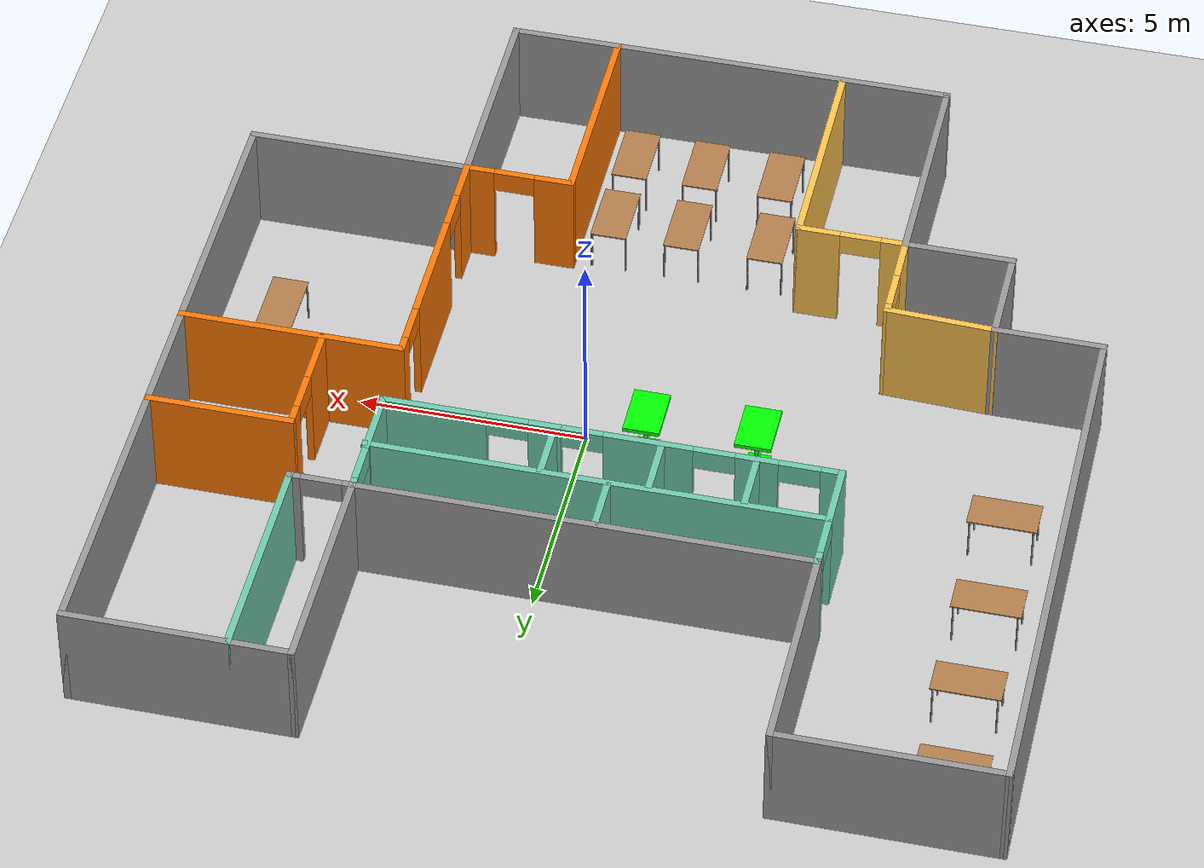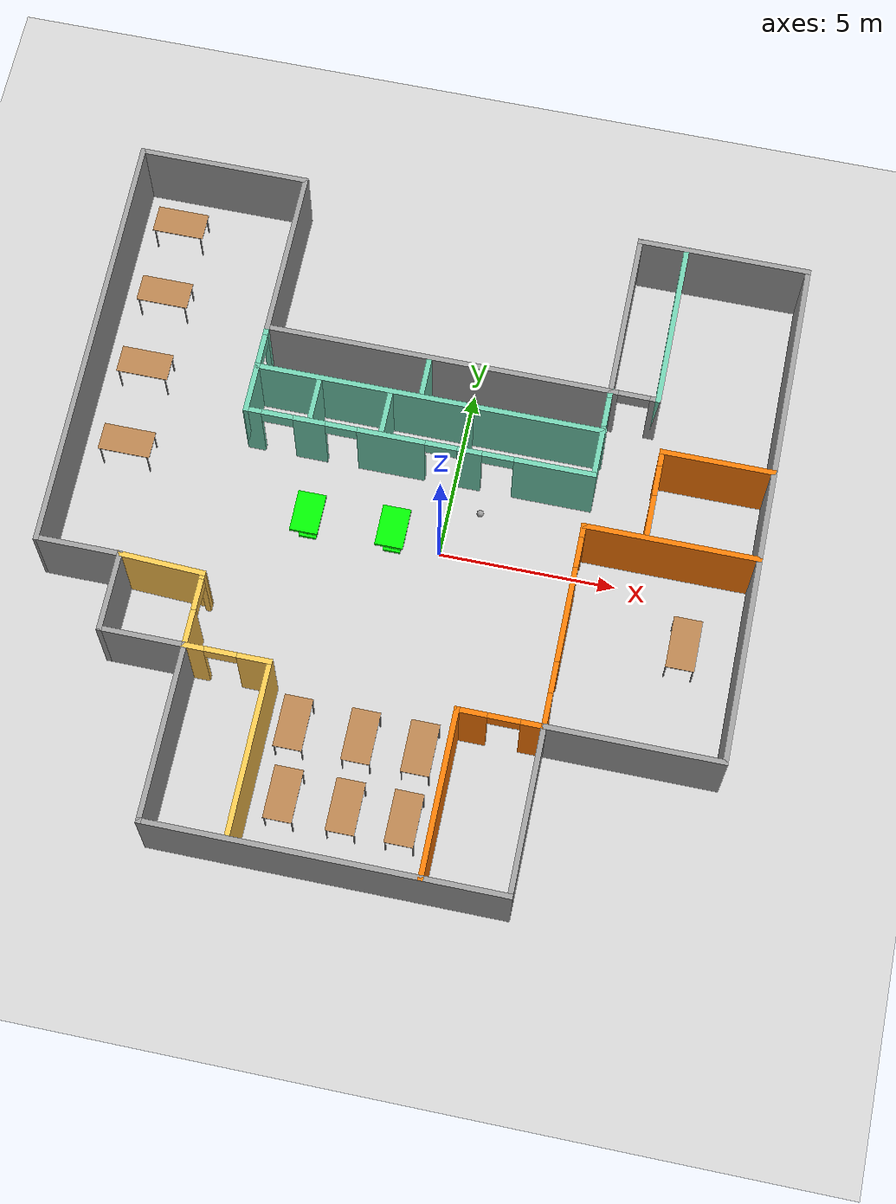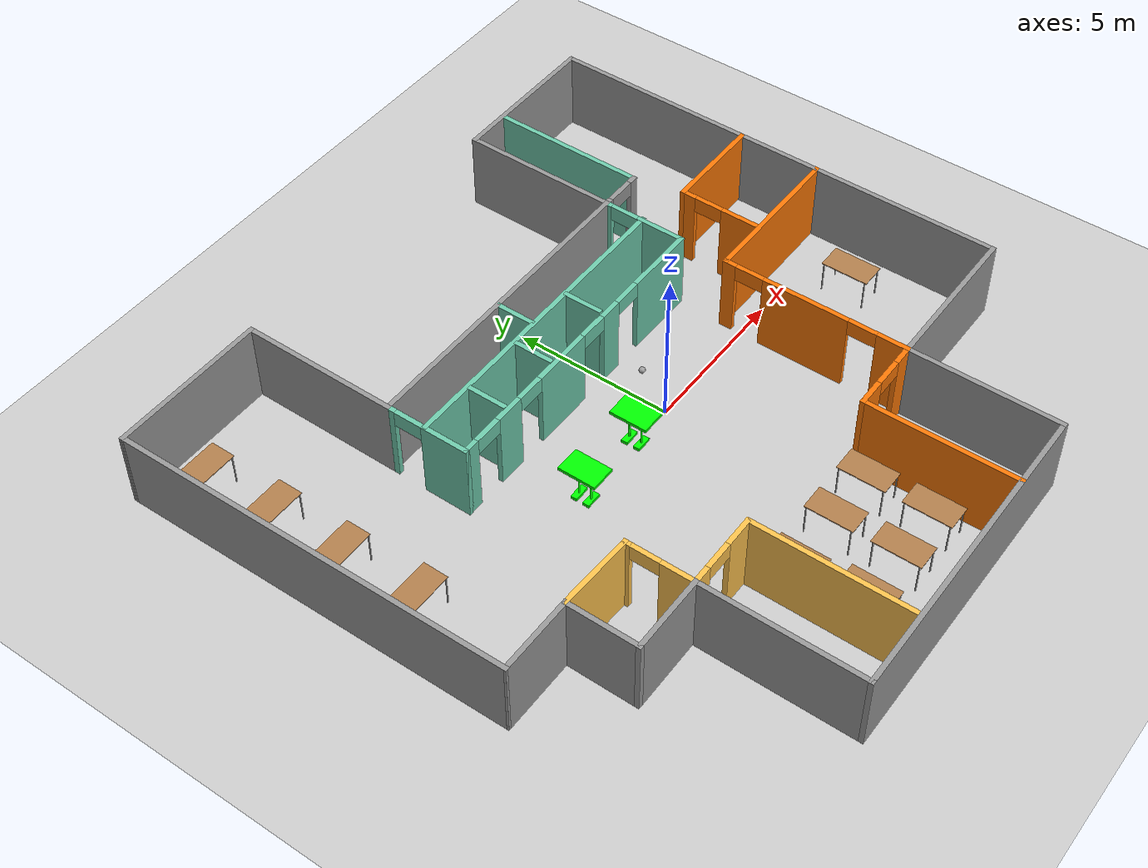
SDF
<sdf version="1.6">
 <world name="default">
  <plugin name="welcome" filename="libwelcome.so"/>
  <light name="sun" type="directional">
   <pose>0 0 10 0 -0 0</pose>
   <diffuse>0.8 0.8 0.8 1</diffuse>
   <specular>0.2 0.2 0.2 1</specular>
   <attenuation>
    <range>1000</range>
    <constant>0.9</constant>
    <linear>0.01</linear>
    <quadratic>0.001</quadratic>
   </attenuation>
   <direction>-0.5 0.1 -0.9</direction>
  </light>
  <model name="ground_plane">
   <static>1</static>
   <link name="link">
    <collision name="collision">
     <geometry><plane><normal>0 0 1</normal><size>100 100</size></plane></geometry>
     <surface>
      <contact><collide_bitmask>65535</collide_bitmask></contact>
      <friction><ode><mu>100</mu><mu2>50</mu2></ode></friction>
     </surface>
    </collision>
    <visual name="visual">
     <cast_shadows>0</cast_shadows>
     <geometry><plane><normal>0 0 1</normal><size>100 100</size></plane></geometry>
     <material>
      <script><uri>file://media/materials/scripts/gazebo.material</uri><name>Gazebo/Grey</name></script>
     </material>
    </visual>
   </link>
  </model>
  <gravity>0 0 -9.8</gravity>
  <magnetic_field>6e-06 2.3e-05 -4.2e-05</magnetic_field>
  <atmosphere type="adiabatic"/>
  <physics name="default_physics" default="0" type="ode">
   <max_step_size>0.001</max_step_size>
   <real_time_factor>1</real_time_factor>
   <real_time_update_rate>1000</real_time_update_rate>
  </physics>
  <scene><ambient>0.4 0.4 0.4 1</ambient><background>0.7 0.7 0.7 1</background><shadows>1</shadows></scene>
  <spherical_coordinates>
   <surface_model>EARTH_WGS84</surface_model>
   <latitude_deg>0</latitude_deg>
   <longitude_deg>0</longitude_deg>
   <elevation>0</elevation>
   <heading_deg>0</heading_deg>
  </spherical_coordinates>
  <model name="building">
   <pose>-1.05602 -0.10222 0 0 -0 0</pose>
   <link name="Wall_0">
    <collision name="Wall_0_Collision">
     <geometry><box><size>5 0.15 2.5</size></box></geometry>
     <pose>0 0 1.25 0 -0 0</pose>
    </collision>
    <visual name="Wall_0_Visual">
     <pose>0 0 1.25 0 -0 0</pose>
     <geometry><box><size>5 0.15 2.5</size></box></geometry>
     <material>
      <script><uri>file://media/materials/scripts/gazebo.material</uri><name>Gazebo/Grey</name></script>
      <ambient>1 1 1 1</ambient>
     </material>
     <meta><layer>0</layer></meta>
    </visual>
    <pose>-7.34955 9.75605 0 0 -0 0</pose>
   </link>
   <link name="Wall_1">
    <collision name="Wall_1_Collision">
     <geometry><box><size>5 0.15 2.5</size></box></geometry>
     <pose>0 0 1.25 0 -0 0</pose>
    </collision>
    <visual name="Wall_1_Visual">
     <pose>0 0 1.25 0 -0 0</pose>
     <geometry><box><size>5 0.15 2.5</size></box></geometry>
     <material>
      <script><uri>file://media/materials/scripts/gazebo.material</uri><name>Gazebo/Grey</name></script>
      <ambient>1 1 1 1</ambient>
     </material>
     <meta><layer>0</layer></meta>
    </visual>
    <pose>-4.92455 7.33105 0 0 0 -1.5708</pose>
   </link>
   <link name="Wall_10">
    <collision name="Wall_10_Collision">
     <geometry><box><size>2.5 0.15 2.5</size></box></geometry>
     <pose>0 0 1.25 0 -0 0</pose>
    </collision>
    <visual name="Wall_10_Visual">
     <pose>0 0 1.25 0 -0 0</pose>
     <geometry><box><size>2.5 0.15 2.5</size></box></geometry>
     <material>
      <script><uri>file://media/materials/scripts/gazebo.material</uri><name>Gazebo/Grey</name></script>
      <ambient>1 1 1 1</ambient>
     </material>
     <meta><layer>0</layer></meta>
    </visual>
    <pose>-6.09955 -4.81295 0 0 -0 3.14159</pose>
   </link>
   <link name="Wall_11">
    <collision name="Wall_11_Collision">
     <geometry><box><size>2.344 0.15 2.5</size></box></geometry>
     <pose>0 0 1.25 0 -0 0</pose>
    </collision>
    <visual name="Wall_11_Visual">
     <pose>0 0 1.25 0 -0 0</pose>
     <geometry><box><size>2.344 0.15 2.5</size></box></geometry>
     <material>
      <script><uri>file://media/materials/scripts/gazebo.material</uri><name>Gazebo/Grey</name></script>
      <ambient>1 1 1 1</ambient>
     </material>
     <meta><layer>0</layer></meta>
    </visual>
    <pose>-7.27455 -3.71595 0 0 -0 1.5708</pose>
   </link>
   <link name="Wall_12">
    <collision name="Wall_12_Collision">
     <geometry><box><size>2.5 0.15 2.5</size></box></geometry>
     <pose>0 0 1.25 0 -0 0</pose>
    </collision>
    <visual name="Wall_12_Visual">
     <pose>0 0 1.25 0 -0 0</pose>
     <geometry><box><size>2.5 0.15 2.5</size></box></geometry>
     <material>
      <script><uri>file://media/materials/scripts/gazebo.material</uri><name>Gazebo/Grey</name></script>
      <ambient>1 1 1 1</ambient>
     </material>
     <meta><layer>0</layer></meta>
    </visual>
    <pose>-8.44955 -2.61895 0 0 -0 3.14159</pose>
   </link>
   <link name="Wall_13">
    <collision name="Wall_13_Collision">
     <geometry><box><size>12.5259 0.15 2.5</size></box></geometry>
     <pose>0 0 1.25 0 -0 0</pose>
    </collision>
    <visual name="Wall_13_Visual">
     <pose>0 0 1.25 0 -0 0</pose>
     <geometry><box><size>12.5259 0.15 2.5</size></box></geometry>
     <material>
      <script><uri>file://media/materials/scripts/gazebo.material</uri><name>Gazebo/Grey</name></script>
      <ambient>1 1 1 1</ambient>
     </material>
     <meta><layer>0</layer></meta>
    </visual>
    <pose>-9.69955 3.56855 0 0 -0 1.58292</pose>
   </link>
   <link name="Wall_15">
    <pose>-3.74955 -4.81295 0 0 -0 0</pose>
    <visual name="Wall_15_Visual_0">
     <pose>-0.942883 0 1.25 0 -0 0</pose>
     <geometry><box><size>0.614234 0.15 2.5</size></box></geometry>
     <material>
      <script><uri>file://media/materials/scripts/gazebo.material</uri><name>Gazebo/Grey</name></script>
      <ambient>1 0.764706 0.305882 1</ambient>
     </material>
     <meta><layer>0</layer></meta>
    </visual>
    <collision name="Wall_15_Collision_0">
     <geometry><box><size>0.614234 0.15 2.5</size></box></geometry>
     <pose>-0.942883 0 1.25 0 -0 0</pose>
    </collision>
    <visual name="Wall_15_Visual_1">
     <pose>0.757117 0 1.25 0 -0 0</pose>
     <geometry><box><size>0.985766 0.15 2.5</size></box></geometry>
     <material>
      <script><uri>file://media/materials/scripts/gazebo.material</uri><name>Gazebo/Grey</name></script>
      <ambient>1 0.764706 0.305882 1</ambient>
     </material>
     <meta><layer>0</layer></meta>
    </visual>
    <collision name="Wall_15_Collision_1">
     <geometry><box><size>0.985766 0.15 2.5</size></box></geometry>
     <pose>0.757117 0 1.25 0 -0 0</pose>
    </collision>
    <visual name="Wall_15_Visual_2">
     <pose>-0.185766 0 2.25 0 -0 0</pose>
     <geometry><box><size>0.9 0.15 0.5</size></box></geometry>
     <material>
      <script><uri>file://media/materials/scripts/gazebo.material</uri><name>Gazebo/Grey</name></script>
      <ambient>1 0.764706 0.305882 1</ambient>
     </material>
     <meta><layer>0</layer></meta>
    </visual>
    <collision name="Wall_15_Collision_2">
     <geometry><box><size>0.9 0.15 0.5</size></box></geometry>
     <pose>-0.185766 0 2.25 0 -0 0</pose>
    </collision>
   </link>
   <link name="Wall_16">
    <collision name="Wall_16_Collision">
     <geometry><box><size>5 0.15 2.5</size></box></geometry>
     <pose>0 0 1.25 0 -0 0</pose>
    </collision>
    <visual name="Wall_16_Visual">
     <pose>0 0 1.25 0 -0 0</pose>
     <geometry><box><size>5 0.15 2.5</size></box></geometry>
     <material>
      <script><uri>file://media/materials/scripts/gazebo.material</uri><name>Gazebo/Grey</name></script>
      <ambient>1 0.764706 0.305882 1</ambient>
     </material>
     <meta><layer>0</layer></meta>
    </visual>
    <pose>-2.57455 -7.23795 0 0 0 -1.5708</pose>
   </link>
   <link name="Wall_18">
    <pose>3.75045 -5.09395 0 0 -0 3.14159</pose>
    <visual name="Wall_18_Visual_0">
     <pose>-0.900353 0 1.25 0 -0 0</pose>
     <geometry><box><size>0.699294 0.15 2.5</size></box></geometry>
     <material>
      <script><uri>file://media/materials/scripts/gazebo.material</uri><name>Gazebo/Grey</name></script>
      <ambient>0.996078 0.47451 0.0196078 1</ambient>
     </material>
     <meta><layer>0</layer></meta>
    </visual>
    <collision name="Wall_18_Collision_0">
     <geometry><box><size>0.699294 0.15 2.5</size></box></geometry>
     <pose>-0.900353 0 1.25 0 -0 0</pose>
    </collision>
    <visual name="Wall_18_Visual_1">
     <pose>0.799647 0 1.25 0 -0 0</pose>
     <geometry><box><size>0.900706 0.15 2.5</size></box></geometry>
     <material>
      <script><uri>file://media/materials/scripts/gazebo.material</uri><name>Gazebo/Grey</name></script>
      <ambient>0.996078 0.47451 0.0196078 1</ambient>
     </material>
     <meta><layer>0</layer></meta>
    </visual>
    <collision name="Wall_18_Collision_1">
     <geometry><box><size>0.900706 0.15 2.5</size></box></geometry>
     <pose>0.799647 0 1.25 0 -0 0</pose>
    </collision>
    <visual name="Wall_18_Visual_2">
     <pose>-0.100706 0 2.25 0 -0 0</pose>
     <geometry><box><size>0.9 0.15 0.5</size></box></geometry>
     <material>
      <script><uri>file://media/materials/scripts/gazebo.material</uri><name>Gazebo/Grey</name></script>
      <ambient>0.996078 0.47451 0.0196078 1</ambient>
     </material>
     <meta><layer>0</layer></meta>
    </visual>
    <collision name="Wall_18_Collision_2">
     <geometry><box><size>0.9 0.15 0.5</size></box></geometry>
     <pose>-0.100706 0 2.25 0 -0 0</pose>
    </collision>
   </link>
   <link name="Wall_2">
    <collision name="Wall_2_Collision">
     <geometry><box><size>10 0.15 2.5</size></box></geometry>
     <pose>0 0 1.25 0 -0 0</pose>
    </collision>
    <visual name="Wall_2_Visual">
     <pose>0 0 1.25 0 -0 0</pose>
     <geometry><box><size>10 0.15 2.5</size></box></geometry>
     <material>
      <script><uri>file://media/materials/scripts/gazebo.material</uri><name>Gazebo/Grey</name></script>
      <ambient>1 1 1 1</ambient>
     </material>
     <meta><layer>0</layer></meta>
    </visual>
    <pose>0.000451 4.90605 0 0 -0 0</pose>
   </link>
   <link name="Wall_21">
    <collision name="Wall_21_Collision">
     <geometry><box><size>4.813 0.15 2.5</size></box></geometry>
     <pose>0 0 1.25 0 -0 0</pose>
    </collision>
    <visual name="Wall_21_Visual">
     <pose>0 0 1.25 0 -0 0</pose>
     <geometry><box><size>4.813 0.15 2.5</size></box></geometry>
     <material>
      <script><uri>file://media/materials/scripts/gazebo.material</uri><name>Gazebo/Grey</name></script>
      <ambient>0.996078 0.47451 0.0196078 1</ambient>
     </material>
     <meta><layer>0</layer></meta>
    </visual>
    <pose>2.57545 -7.42545 0 0 0 -1.5708</pose>
   </link>
   <link name="Wall_23">
    <pose>-4.92455 -3.76295 0 0 -0 1.5708</pose>
    <visual name="Wall_23_Visual_0">
     <pose>-0.57792 0 1.25 0 -0 0</pose>
     <geometry><box><size>1.09416 0.15 2.5</size></box></geometry>
     <material>
      <script><uri>file://media/materials/scripts/gazebo.material</uri><name>Gazebo/Grey</name></script>
      <ambient>1 0.764706 0.305882 1</ambient>
     </material>
     <meta><layer>0</layer></meta>
    </visual>
    <collision name="Wall_23_Collision_0">
     <geometry><box><size>1.09416 0.15 2.5</size></box></geometry>
     <pose>-0.57792 0 1.25 0 -0 0</pose>
    </collision>
    <visual name="Wall_23_Visual_1">
     <pose>0.99708 0 1.25 0 -0 0</pose>
     <geometry><box><size>0.255839 0.15 2.5</size></box></geometry>
     <material>
      <script><uri>file://media/materials/scripts/gazebo.material</uri><name>Gazebo/Grey</name></script>
      <ambient>1 0.764706 0.305882 1</ambient>
     </material>
     <meta><layer>0</layer></meta>
    </visual>
    <collision name="Wall_23_Collision_1">
     <geometry><box><size>0.255839 0.15 2.5</size></box></geometry>
     <pose>0.99708 0 1.25 0 -0 0</pose>
    </collision>
    <visual name="Wall_23_Visual_2">
     <pose>0.419161 0 2.25 0 -0 0</pose>
     <geometry><box><size>0.9 0.15 0.5</size></box></geometry>
     <material>
      <script><uri>file://media/materials/scripts/gazebo.material</uri><name>Gazebo/Grey</name></script>
      <ambient>1 0.764706 0.305882 1</ambient>
     </material>
     <meta><layer>0</layer></meta>
    </visual>
    <collision name="Wall_23_Collision_2">
     <geometry><box><size>0.9 0.15 0.5</size></box></geometry>
     <pose>0.419161 0 2.25 0 -0 0</pose>
    </collision>
   </link>
   <link name="Wall_24">
    <collision name="Wall_24_Collision">
     <geometry><box><size>2.50188 0.15 2.5</size></box></geometry>
     <pose>0 0 1.25 0 -0 0</pose>
    </collision>
    <visual name="Wall_24_Visual">
     <pose>0 0 1.25 0 -0 0</pose>
     <geometry><box><size>2.50188 0.15 2.5</size></box></geometry>
     <material>
      <script><uri>file://media/materials/scripts/gazebo.material</uri><name>Gazebo/Grey</name></script>
      <ambient>1 0.764706 0.305882 1</ambient>
     </material>
     <meta><layer>0</layer></meta>
    </visual>
    <pose>-6.09955 -2.66595 0 0 -0 3.10161</pose>
   </link>
   <link name="Wall_26">
    <pose>4.92545 -2.16895 0 0 -0 1.5708</pose>
    <visual name="Wall_26_Visual_0">
     <pose>-2.49069 0 1.25 0 -0 0</pose>
     <geometry><box><size>1.01863 0.15 2.5</size></box></geometry>
     <material>
      <script><uri>file://media/materials/scripts/gazebo.material</uri><name>Gazebo/Grey</name></script>
      <ambient>0.996078 0.47451 0.0196078 1</ambient>
     </material>
     <meta><layer>0</layer></meta>
    </visual>
    <collision name="Wall_26_Collision_0">
     <geometry><box><size>1.01863 0.15 2.5</size></box></geometry>
     <pose>-2.49069 0 1.25 0 -0 0</pose>
    </collision>
    <visual name="Wall_26_Visual_1">
     <pose>0.299469 0 1.25 0 -0 0</pose>
     <geometry><box><size>2.76168 0.15 2.5</size></box></geometry>
     <material>
      <script><uri>file://media/materials/scripts/gazebo.material</uri><name>Gazebo/Grey</name></script>
      <ambient>0.996078 0.47451 0.0196078 1</ambient>
     </material>
     <meta><layer>0</layer></meta>
    </visual>
    <collision name="Wall_26_Collision_1">
     <geometry><box><size>2.76168 0.15 2.5</size></box></geometry>
     <pose>0.299469 0 1.25 0 -0 0</pose>
    </collision>
    <visual name="Wall_26_Visual_2">
     <pose>2.79015 0 1.25 0 -0 0</pose>
     <geometry><box><size>0.419692 0.15 2.5</size></box></geometry>
     <material>
      <script><uri>file://media/materials/scripts/gazebo.material</uri><name>Gazebo/Grey</name></script>
      <ambient>0.996078 0.47451 0.0196078 1</ambient>
     </material>
     <meta><layer>0</layer></meta>
    </visual>
    <collision name="Wall_26_Collision_2">
     <geometry><box><size>0.419692 0.15 2.5</size></box></geometry>
     <pose>2.79015 0 1.25 0 -0 0</pose>
    </collision>
    <visual name="Wall_26_Visual_3">
     <pose>-1.53137 0 2.25 0 -0 0</pose>
     <geometry><box><size>0.9 0.15 0.5</size></box></geometry>
     <material>
      <script><uri>file://media/materials/scripts/gazebo.material</uri><name>Gazebo/Grey</name></script>
      <ambient>0.996078 0.47451 0.0196078 1</ambient>
     </material>
     <meta><layer>0</layer></meta>
    </visual>
    <collision name="Wall_26_Collision_3">
     <geometry><box><size>0.9 0.15 0.5</size></box></geometry>
     <pose>-1.53137 0 2.25 0 -0 0</pose>
    </collision>
    <visual name="Wall_26_Visual_4">
     <pose>2.13031 0 2.25 0 -0 0</pose>
     <geometry><box><size>0.9 0.15 0.5</size></box></geometry>
     <material>
      <script><uri>file://media/materials/scripts/gazebo.material</uri><name>Gazebo/Grey</name></script>
      <ambient>0.996078 0.47451 0.0196078 1</ambient>
     </material>
     <meta><layer>0</layer></meta>
    </visual>
    <collision name="Wall_26_Collision_4">
     <geometry><box><size>0.9 0.15 0.5</size></box></geometry>
     <pose>2.13031 0 2.25 0 -0 0</pose>
    </collision>
   </link>
   <link name="Wall_27">
    <collision name="Wall_27_Collision">
     <geometry><box><size>5 0.15 2.5</size></box></geometry>
     <pose>0 0 1.25 0 -0 0</pose>
    </collision>
    <visual name="Wall_27_Visual">
     <pose>0 0 1.25 0 -0 0</pose>
     <geometry><box><size>5 0.15 2.5</size></box></geometry>
     <material>
      <script><uri>file://media/materials/scripts/gazebo.material</uri><name>Gazebo/Grey</name></script>
      <ambient>0.996078 0.47451 0.0196078 1</ambient>
     </material>
     <meta><layer>0</layer></meta>
    </visual>
    <pose>7.35045 0.756049 0 0 -0 0</pose>
   </link>
   <link name="Wall_29">
    <pose>6.65238 2.07506 0 0 -0 1.5708</pose>
    <visual name="Wall_29_Visual_0">
     <pose>-0.708109 0 1.25 0 -0 0</pose>
     <geometry><box><size>1.33378 0.15 2.5</size></box></geometry>
     <material>
      <script><uri>file://media/materials/scripts/gazebo.material</uri><name>Gazebo/Grey</name></script>
      <ambient>0.996078 0.47451 0.0196078 1</ambient>
     </material>
     <meta><layer>0</layer></meta>
    </visual>
    <collision name="Wall_29_Collision_0">
     <geometry><box><size>1.33378 0.15 2.5</size></box></geometry>
     <pose>-0.708109 0 1.25 0 -0 0</pose>
    </collision>
    <visual name="Wall_29_Visual_1">
     <pose>1.11689 0 1.25 0 -0 0</pose>
     <geometry><box><size>0.516217 0.15 2.5</size></box></geometry>
     <material>
      <script><uri>file://media/materials/scripts/gazebo.material</uri><name>Gazebo/Grey</name></script>
      <ambient>0.996078 0.47451 0.0196078 1</ambient>
     </material>
     <meta><layer>0</layer></meta>
    </visual>
    <collision name="Wall_29_Collision_1">
     <geometry><box><size>0.516217 0.15 2.5</size></box></geometry>
     <pose>1.11689 0 1.25 0 -0 0</pose>
    </collision>
    <visual name="Wall_29_Visual_2">
     <pose>0.408783 0 2.25 0 -0 0</pose>
     <geometry><box><size>0.9 0.15 0.5</size></box></geometry>
     <material>
      <script><uri>file://media/materials/scripts/gazebo.material</uri><name>Gazebo/Grey</name></script>
      <ambient>0.996078 0.47451 0.0196078 1</ambient>
     </material>
     <meta><layer>0</layer></meta>
    </visual>
    <collision name="Wall_29_Collision_2">
     <geometry><box><size>0.9 0.15 0.5</size></box></geometry>
     <pose>0.408783 0 2.25 0 -0 0</pose>
    </collision>
   </link>
   <link name="Wall_3">
    <collision name="Wall_3_Collision">
     <geometry><box><size>5 0.15 2.5</size></box></geometry>
     <pose>0 0 1.25 0 -0 0</pose>
    </collision>
    <visual name="Wall_3_Visual">
     <pose>0 0 1.25 0 -0 0</pose>
     <geometry><box><size>5 0.15 2.5</size></box></geometry>
     <material>
      <script><uri>file://media/materials/scripts/gazebo.material</uri><name>Gazebo/Grey</name></script>
      <ambient>1 1 1 1</ambient>
     </material>
     <meta><layer>0</layer></meta>
    </visual>
    <pose>4.92545 7.33105 0 0 -0 1.5708</pose>
   </link>
   <link name="Wall_30">
    <collision name="Wall_30_Collision">
     <geometry><box><size>3.25 0.15 2.5</size></box></geometry>
     <pose>0 0 1.25 0 -0 0</pose>
    </collision>
    <visual name="Wall_30_Visual">
     <pose>0 0 1.25 0 -0 0</pose>
     <geometry><box><size>3.25 0.15 2.5</size></box></geometry>
     <material>
      <script><uri>file://media/materials/scripts/gazebo.material</uri><name>Gazebo/Grey</name></script>
      <ambient>0.996078 0.47451 0.0196078 1</ambient>
     </material>
     <meta><layer>0</layer></meta>
    </visual>
    <pose>8.20237 3.37506 0 0 -0 0</pose>
   </link>
   <link name="Wall_32">
    <pose>5.60045 4.90605 0 0 -0 0</pose>
    <visual name="Wall_32_Visual_0">
     <pose>-0.605415 0 1.25 0 -0 0</pose>
     <geometry><box><size>0.289171 0.15 2.5</size></box></geometry>
     <material>
      <script><uri>file://media/materials/scripts/gazebo.material</uri><name>Gazebo/Grey</name></script>
      <ambient>1 1 1 1</ambient>
     </material>
     <meta><layer>0</layer></meta>
    </visual>
    <collision name="Wall_32_Collision_0">
     <geometry><box><size>0.289171 0.15 2.5</size></box></geometry>
     <pose>-0.605415 0 1.25 0 -0 0</pose>
    </collision>
    <visual name="Wall_32_Visual_1">
     <pose>0.594585 0 1.25 0 -0 0</pose>
     <geometry><box><size>0.310829 0.15 2.5</size></box></geometry>
     <material>
      <script><uri>file://media/materials/scripts/gazebo.material</uri><name>Gazebo/Grey</name></script>
      <ambient>1 1 1 1</ambient>
     </material>
     <meta><layer>0</layer></meta>
    </visual>
    <collision name="Wall_32_Collision_1">
     <geometry><box><size>0.310829 0.15 2.5</size></box></geometry>
     <pose>0.594585 0 1.25 0 -0 0</pose>
    </collision>
    <visual name="Wall_32_Visual_2">
     <pose>-0.010829 0 2.25 0 -0 0</pose>
     <geometry><box><size>0.9 0.15 0.5</size></box></geometry>
     <material>
      <script><uri>file://media/materials/scripts/gazebo.material</uri><name>Gazebo/Grey</name></script>
      <ambient>1 1 1 1</ambient>
     </material>
     <meta><layer>0</layer></meta>
    </visual>
    <collision name="Wall_32_Collision_2">
     <geometry><box><size>0.9 0.15 0.5</size></box></geometry>
     <pose>-0.010829 0 2.25 0 -0 0</pose>
    </collision>
   </link>
   <link name="Wall_33">
    <collision name="Wall_33_Collision">
     <geometry><box><size>5 0.15 2.5</size></box></geometry>
     <pose>0 0 1.25 0 -0 0</pose>
    </collision>
    <visual name="Wall_33_Visual">
     <pose>0 0 1.25 0 -0 0</pose>
     <geometry><box><size>5 0.15 2.5</size></box></geometry>
     <material>
      <script><uri>file://media/materials/scripts/gazebo.material</uri><name>Gazebo/Grey</name></script>
      <ambient>0.435294 0.796078 0.67451 1</ambient>
     </material>
     <meta><layer>0</layer></meta>
    </visual>
    <pose>6.27545 7.33105 0 0 -0 1.5708</pose>
   </link>
   <link name="Wall_35">
    <pose>-4.92455 3.60605 0 0 0 -1.5708</pose>
    <visual name="Wall_35_Visual_0">
     <pose>-1.20915 0 1.25 0 -0 0</pose>
     <geometry><box><size>0.3317 0.15 2.5</size></box></geometry>
     <material>
      <script><uri>file://media/materials/scripts/gazebo.material</uri><name>Gazebo/Grey</name></script>
      <ambient>0.435294 0.796078 0.67451 1</ambient>
     </material>
     <meta><layer>0</layer></meta>
    </visual>
    <collision name="Wall_35_Collision_0">
     <geometry><box><size>0.3317 0.15 2.5</size></box></geometry>
     <pose>-1.20915 0 1.25 0 -0 0</pose>
    </collision>
    <visual name="Wall_35_Visual_1">
     <pose>0.61585 0 1.25 0 -0 0</pose>
     <geometry><box><size>1.5183 0.15 2.5</size></box></geometry>
     <material>
      <script><uri>file://media/materials/scripts/gazebo.material</uri><name>Gazebo/Grey</name></script>
      <ambient>0.435294 0.796078 0.67451 1</ambient>
     </material>
     <meta><layer>0</layer></meta>
    </visual>
    <collision name="Wall_35_Collision_1">
     <geometry><box><size>1.5183 0.15 2.5</size></box></geometry>
     <pose>0.61585 0 1.25 0 -0 0</pose>
    </collision>
    <visual name="Wall_35_Visual_2">
     <pose>-0.5933 0 2.25 0 -0 0</pose>
     <geometry><box><size>0.9 0.15 0.5</size></box></geometry>
     <material>
      <script><uri>file://media/materials/scripts/gazebo.material</uri><name>Gazebo/Grey</name></script>
      <ambient>0.435294 0.796078 0.67451 1</ambient>
     </material>
     <meta><layer>0</layer></meta>
    </visual>
    <collision name="Wall_35_Collision_2">
     <geometry><box><size>0.9 0.15 0.5</size></box></geometry>
     <pose>-0.5933 0 2.25 0 -0 0</pose>
    </collision>
   </link>
   <link name="Wall_36">
    <pose>0.000451 2.30605 0 0 -0 0</pose>
    <visual name="Wall_36_Visual_0">
     <pose>-4.74054 0 1.25 0 -0 0</pose>
     <geometry><box><size>0.518918 0.15 2.5</size></box></geometry>
     <material>
      <script><uri>file://media/materials/scripts/gazebo.material</uri><name>Gazebo/Grey</name></script>
      <ambient>0.435294 0.796078 0.67451 1</ambient>
     </material>
     <meta><layer>0</layer></meta>
    </visual>
    <collision name="Wall_36_Collision_0">
     <geometry><box><size>0.518918 0.15 2.5</size></box></geometry>
     <pose>-4.74054 0 1.25 0 -0 0</pose>
    </collision>
    <visual name="Wall_36_Visual_1">
     <pose>-3.12154 0 1.25 0 -0 0</pose>
     <geometry><box><size>0.919085 0.15 2.5</size></box></geometry>
     <material>
      <script><uri>file://media/materials/scripts/gazebo.material</uri><name>Gazebo/Grey</name></script>
      <ambient>0.435294 0.796078 0.67451 1</ambient>
     </material>
     <meta><layer>0</layer></meta>
    </visual>
    <collision name="Wall_36_Collision_1">
     <geometry><box><size>0.919085 0.15 2.5</size></box></geometry>
     <pose>-3.12154 0 1.25 0 -0 0</pose>
    </collision>
    <visual name="Wall_36_Visual_2">
     <pose>-0.79418 0 1.25 0 -0 0</pose>
     <geometry><box><size>1.93563 0.15 2.5</size></box></geometry>
     <material>
      <script><uri>file://media/materials/scripts/gazebo.material</uri><name>Gazebo/Grey</name></script>
      <ambient>0.435294 0.796078 0.67451 1</ambient>
     </material>
     <meta><layer>0</layer></meta>
    </visual>
    <collision name="Wall_36_Collision_2">
     <geometry><box><size>1.93563 0.15 2.5</size></box></geometry>
     <pose>-0.79418 0 1.25 0 -0 0</pose>
    </collision>
    <visual name="Wall_36_Visual_3">
     <pose>1.42617 0 1.25 0 -0 0</pose>
     <geometry><box><size>0.705075 0.15 2.5</size></box></geometry>
     <material>
      <script><uri>file://media/materials/scripts/gazebo.material</uri><name>Gazebo/Grey</name></script>
      <ambient>0.435294 0.796078 0.67451 1</ambient>
     </material>
     <meta><layer>0</layer></meta>
    </visual>
    <collision name="Wall_36_Collision_3">
     <geometry><box><size>0.705075 0.15 2.5</size></box></geometry>
     <pose>1.42617 0 1.25 0 -0 0</pose>
    </collision>
    <visual name="Wall_36_Visual_4">
     <pose>3.83935 0 1.25 0 -0 0</pose>
     <geometry><box><size>2.32129 0.15 2.5</size></box></geometry>
     <material>
      <script><uri>file://media/materials/scripts/gazebo.material</uri><name>Gazebo/Grey</name></script>
      <ambient>0.435294 0.796078 0.67451 1</ambient>
     </material>
     <meta><layer>0</layer></meta>
    </visual>
    <collision name="Wall_36_Collision_4">
     <geometry><box><size>2.32129 0.15 2.5</size></box></geometry>
     <pose>3.83935 0 1.25 0 -0 0</pose>
    </collision>
    <visual name="Wall_36_Visual_5">
     <pose>-4.03108 0 2.25 0 -0 0</pose>
     <geometry><box><size>0.9 0.15 0.5</size></box></geometry>
     <material>
      <script><uri>file://media/materials/scripts/gazebo.material</uri><name>Gazebo/Grey</name></script>
      <ambient>0.435294 0.796078 0.67451 1</ambient>
     </material>
     <meta><layer>0</layer></meta>
    </visual>
    <collision name="Wall_36_Collision_5">
     <geometry><box><size>0.9 0.15 0.5</size></box></geometry>
     <pose>-4.03108 0 2.25 0 -0 0</pose>
    </collision>
    <visual name="Wall_36_Visual_6">
     <pose>-2.212 0 2.25 0 -0 0</pose>
     <geometry><box><size>0.9 0.15 0.5</size></box></geometry>
     <material>
      <script><uri>file://media/materials/scripts/gazebo.material</uri><name>Gazebo/Grey</name></script>
      <ambient>0.435294 0.796078 0.67451 1</ambient>
     </material>
     <meta><layer>0</layer></meta>
    </visual>
    <collision name="Wall_36_Collision_6">
     <geometry><box><size>0.9 0.15 0.5</size></box></geometry>
     <pose>-2.212 0 2.25 0 -0 0</pose>
    </collision>
    <visual name="Wall_36_Visual_7">
     <pose>0.623636 0 2.25 0 -0 0</pose>
     <geometry><box><size>0.9 0.15 0.5</size></box></geometry>
     <material>
      <script><uri>file://media/materials/scripts/gazebo.material</uri><name>Gazebo/Grey</name></script>
      <ambient>0.435294 0.796078 0.67451 1</ambient>
     </material>
     <meta><layer>0</layer></meta>
    </visual>
    <collision name="Wall_36_Collision_7">
     <geometry><box><size>0.9 0.15 0.5</size></box></geometry>
     <pose>0.623636 0 2.25 0 -0 0</pose>
    </collision>
    <visual name="Wall_36_Visual_8">
     <pose>2.22871 0 2.25 0 -0 0</pose>
     <geometry><box><size>0.9 0.15 0.5</size></box></geometry>
     <material>
      <script><uri>file://media/materials/scripts/gazebo.material</uri><name>Gazebo/Grey</name></script>
      <ambient>0.435294 0.796078 0.67451 1</ambient>
     </material>
     <meta><layer>0</layer></meta>
    </visual>
    <collision name="Wall_36_Collision_8">
     <geometry><box><size>0.9 0.15 0.5</size></box></geometry>
     <pose>2.22871 0 2.25 0 -0 0</pose>
    </collision>
   </link>
   <link name="Wall_37">
    <pose>4.92545 3.60605 0 0 -0 1.5708</pose>
    <visual name="Wall_37_Visual_0">
     <pose>-0.589099 0 1.25 0 -0 0</pose>
     <geometry><box><size>1.5718 0.15 2.5</size></box></geometry>
     <material>
      <script><uri>file://media/materials/scripts/gazebo.material</uri><name>Gazebo/Grey</name></script>
      <ambient>0.435294 0.796078 0.67451 1</ambient>
     </material>
     <meta><layer>0</layer></meta>
    </visual>
    <collision name="Wall_37_Collision_0">
     <geometry><box><size>1.5718 0.15 2.5</size></box></geometry>
     <pose>-0.589099 0 1.25 0 -0 0</pose>
    </collision>
    <visual name="Wall_37_Visual_1">
     <pose>1.2359 0 1.25 0 -0 0</pose>
     <geometry><box><size>0.278198 0.15 2.5</size></box></geometry>
     <material>
      <script><uri>file://media/materials/scripts/gazebo.material</uri><name>Gazebo/Grey</name></script>
      <ambient>0.435294 0.796078 0.67451 1</ambient>
     </material>
     <meta><layer>0</layer></meta>
    </visual>
    <collision name="Wall_37_Collision_1">
     <geometry><box><size>0.278198 0.15 2.5</size></box></geometry>
     <pose>1.2359 0 1.25 0 -0 0</pose>
    </collision>
    <visual name="Wall_37_Visual_2">
     <pose>0.646802 0 2.25 0 -0 0</pose>
     <geometry><box><size>0.9 0.15 0.5</size></box></geometry>
     <material>
      <script><uri>file://media/materials/scripts/gazebo.material</uri><name>Gazebo/Grey</name></script>
      <ambient>0.435294 0.796078 0.67451 1</ambient>
     </material>
     <meta><layer>0</layer></meta>
    </visual>
    <collision name="Wall_37_Collision_2">
     <geometry><box><size>0.9 0.15 0.5</size></box></geometry>
     <pose>0.646802 0 2.25 0 -0 0</pose>
    </collision>
   </link>
   <link name="Wall_39">
    <collision name="Wall_39_Collision">
     <geometry><box><size>10 0.15 2.5</size></box></geometry>
     <pose>0 0 1.25 0 -0 0</pose>
    </collision>
    <visual name="Wall_39_Visual">
     <pose>0 0 1.25 0 -0 0</pose>
     <geometry><box><size>10 0.15 2.5</size></box></geometry>
     <material>
      <script><uri>file://media/materials/scripts/gazebo.material</uri><name>Gazebo/Grey</name></script>
      <ambient>0.435294 0.796078 0.67451 1</ambient>
     </material>
     <meta><layer>0</layer></meta>
    </visual>
    <pose>0.03833 3.66432 0 0 -0 0</pose>
   </link>
   <link name="Wall_4">
    <collision name="Wall_4_Collision">
     <geometry><box><size>5 0.15 2.5</size></box></geometry>
     <pose>0 0 1.25 0 -0 0</pose>
    </collision>
    <visual name="Wall_4_Visual">
     <pose>0 0 1.25 0 -0 0</pose>
     <geometry><box><size>5 0.15 2.5</size></box></geometry>
     <material>
      <script><uri>file://media/materials/scripts/gazebo.material</uri><name>Gazebo/Grey</name></script>
      <ambient>1 1 1 1</ambient>
     </material>
     <meta><layer>0</layer></meta>
    </visual>
    <pose>7.35045 9.75605 0 0 -0 0</pose>
   </link>
   <link name="Wall_41">
    <collision name="Wall_41_Collision">
     <geometry><box><size>1.25 0.15 2.5</size></box></geometry>
     <pose>0 0 1.25 0 -0 0</pose>
    </collision>
    <visual name="Wall_41_Visual">
     <pose>0 0 1.25 0 -0 0</pose>
     <geometry><box><size>1.25 0.15 2.5</size></box></geometry>
     <material>
      <script><uri>file://media/materials/scripts/gazebo.material</uri><name>Gazebo/Grey</name></script>
      <ambient>0.435294 0.796078 0.67451 1</ambient>
     </material>
     <meta><layer>0</layer></meta>
    </visual>
    <pose>-0.231953 4.29138 0 0 0 -1.5708</pose>
   </link>
   <link name="Wall_43">
    <collision name="Wall_43_Collision">
     <geometry><box><size>1.25 0.15 2.5</size></box></geometry>
     <pose>0 0 1.25 0 -0 0</pose>
    </collision>
    <visual name="Wall_43_Visual">
     <pose>0 0 1.25 0 -0 0</pose>
     <geometry><box><size>1.25 0.15 2.5</size></box></geometry>
     <material>
      <script><uri>file://media/materials/scripts/gazebo.material</uri><name>Gazebo/Grey</name></script>
      <ambient>0.435294 0.796078 0.67451 1</ambient>
     </material>
     <meta><layer>0</layer></meta>
    </visual>
    <pose>-3.12109 3.00732 0 0 0 -1.5708</pose>
   </link>
   <link name="Wall_45">
    <collision name="Wall_45_Collision">
     <geometry><box><size>1.25 0.15 2.5</size></box></geometry>
     <pose>0 0 1.25 0 -0 0</pose>
    </collision>
    <visual name="Wall_45_Visual">
     <pose>0 0 1.25 0 -0 0</pose>
     <geometry><box><size>1.25 0.15 2.5</size></box></geometry>
     <material>
      <script><uri>file://media/materials/scripts/gazebo.material</uri><name>Gazebo/Grey</name></script>
      <ambient>0.435294 0.796078 0.67451 1</ambient>
     </material>
     <meta><layer>0</layer></meta>
    </visual>
    <pose>-1.08799 3.00732 0 0 0 -1.5708</pose>
   </link>
   <link name="Wall_47">
    <collision name="Wall_47_Collision">
     <geometry><box><size>1.25 0.15 2.5</size></box></geometry>
     <pose>0 0 1.25 0 -0 0</pose>
    </collision>
    <visual name="Wall_47_Visual">
     <pose>0 0 1.25 0 -0 0</pose>
     <geometry><box><size>1.25 0.15 2.5</size></box></geometry>
     <material>
      <script><uri>file://media/materials/scripts/gazebo.material</uri><name>Gazebo/Grey</name></script>
      <ambient>0.435294 0.796078 0.67451 1</ambient>
     </material>
     <meta><layer>0</layer></meta>
    </visual>
    <pose>1.21261 3.06082 0 0 0 -1.5708</pose>
   </link>
   <link name="Wall_5">
    <collision name="Wall_5_Collision">
     <geometry><box><size>15 0.15 2.5</size></box></geometry>
     <pose>0 0 1.25 0 -0 0</pose>
    </collision>
    <visual name="Wall_5_Visual">
     <pose>0 0 1.25 0 -0 0</pose>
     <geometry><box><size>15 0.15 2.5</size></box></geometry>
     <material>
      <script><uri>file://media/materials/scripts/gazebo.material</uri><name>Gazebo/Grey</name></script>
      <ambient>1 1 1 1</ambient>
     </material>
     <meta><layer>0</layer></meta>
    </visual>
    <pose>9.77545 2.33105 0 0 0 -1.5708</pose>
   </link>
   <link name="Wall_6">
    <collision name="Wall_6_Collision">
     <geometry><box><size>5 0.15 2.5</size></box></geometry>
     <pose>0 0 1.25 0 -0 0</pose>
    </collision>
    <visual name="Wall_6_Visual">
     <pose>0 0 1.25 0 -0 0</pose>
     <geometry><box><size>5 0.15 2.5</size></box></geometry>
     <material>
      <script><uri>file://media/materials/scripts/gazebo.material</uri><name>Gazebo/Grey</name></script>
      <ambient>1 1 1 1</ambient>
     </material>
     <meta><layer>0</layer></meta>
    </visual>
    <pose>7.35045 -5.09395 0 0 -0 3.14159</pose>
   </link>
   <link name="Wall_7">
    <collision name="Wall_7_Collision">
     <geometry><box><size>4.81285 0.15 2.5</size></box></geometry>
     <pose>0 0 1.25 0 -0 0</pose>
    </collision>
    <visual name="Wall_7_Visual">
     <pose>0 0 1.25 0 -0 0</pose>
     <geometry><box><size>4.81285 0.15 2.5</size></box></geometry>
     <material>
      <script><uri>file://media/materials/scripts/gazebo.material</uri><name>Gazebo/Grey</name></script>
      <ambient>1 1 1 1</ambient>
     </material>
     <meta><layer>0</layer></meta>
    </visual>
    <pose>4.92545 -7.42545 0 0 0 -1.5708</pose>
   </link>
   <link name="Wall_8">
    <collision name="Wall_8_Collision">
     <geometry><box><size>10 0.15 2.5</size></box></geometry>
     <pose>0 0 1.25 0 -0 0</pose>
    </collision>
    <visual name="Wall_8_Visual">
     <pose>0 0 1.25 0 -0 0</pose>
     <geometry><box><size>10 0.15 2.5</size></box></geometry>
     <material>
      <script><uri>file://media/materials/scripts/gazebo.material</uri><name>Gazebo/Grey</name></script>
      <ambient>1 1 1 1</ambient>
     </material>
     <meta><layer>0</layer></meta>
    </visual>
    <pose>0.000451 -9.75695 0 0 -0 3.14159</pose>
   </link>
   <link name="Wall_9">
    <collision name="Wall_9_Collision">
     <geometry><box><size>5.09358 0.15 2.5</size></box></geometry>
     <pose>0 0 1.25 0 -0 0</pose>
    </collision>
    <visual name="Wall_9_Visual">
     <pose>0 0 1.25 0 -0 0</pose>
     <geometry><box><size>5.09358 0.15 2.5</size></box></geometry>
     <material>
      <script><uri>file://media/materials/scripts/gazebo.material</uri><name>Gazebo/Grey</name></script>
      <ambient>1 1 1 1</ambient>
     </material>
     <meta><layer>0</layer></meta>
    </visual>
    <pose>-4.92455 -7.28495 0 0 -0 1.5708</pose>
   </link>
   <static>1</static>
  </model>
  <model name="table">
   <static>1</static>
   <link name="link">
    <collision name="surface">
     <pose>0 0 1 0 -0 0</pose>
     <geometry><box><size>1.5 0.8 0.03</size></box></geometry>
     <surface><friction><ode><mu>0.6</mu><mu2>0.6</mu2></ode></friction></surface>
    </collision>
    <visual name="visual1">
     <pose>0 0 1 0 -0 0</pose>
     <geometry><box><size>1.5 0.8 0.03</size></box></geometry>
     <material>
      <script><uri>file://media/materials/scripts/gazebo.material</uri><name>Gazebo/Wood</name></script>
     </material>
    </visual>
    <collision name="front_left_leg">
     <pose>0.68 0.38 0.5 0 -0 0</pose>
     <geometry><cylinder><radius>0.02</radius><length>1</length></cylinder></geometry>
    </collision>
    <visual name="front_left_leg">
     <pose>0.68 0.38 0.5 0 -0 0</pose>
     <geometry><cylinder><radius>0.02</radius><length>1</length></cylinder></geometry>
     <material>
      <script><uri>file://media/materials/scripts/gazebo.material</uri><name>Gazebo/Grey</name></script>
     </material>
    </visual>
    <collision name="front_right_leg">
     <pose>0.68 -0.38 0.5 0 -0 0</pose>
     <geometry><cylinder><radius>0.02</radius><length>1</length></cylinder></geometry>
    </collision>
    <visual name="front_right_leg">
     <pose>0.68 -0.38 0.5 0 -0 0</pose>
     <geometry><cylinder><radius>0.02</radius><length>1</length></cylinder></geometry>
     <material>
      <script><uri>file://media/materials/scripts/gazebo.material</uri><name>Gazebo/Grey</name></script>
     </material>
    </visual>
    <collision name="back_right_leg">
     <pose>-0.68 -0.38 0.5 0 -0 0</pose>
     <geometry><cylinder><radius>0.02</radius><length>1</length></cylinder></geometry>
    </collision>
    <visual name="back_right_leg">
     <pose>-0.68 -0.38 0.5 0 -0 0</pose>
     <geometry><cylinder><radius>0.02</radius><length>1</length></cylinder></geometry>
     <material>
      <script><uri>file://media/materials/scripts/gazebo.material</uri><name>Gazebo/Grey</name></script>
     </material>
    </visual>
    <collision name="back_left_leg">
     <pose>-0.68 0.38 0.5 0 -0 0</pose>
     <geometry><cylinder><radius>0.02</radius><length>1</length></cylinder></geometry>
    </collision>
    <visual name="back_left_leg">
     <pose>-0.68 0.38 0.5 0 -0 0</pose>
     <geometry><cylinder><radius>0.02</radius><length>1</length></cylinder></geometry>
     <material>
      <script><uri>file://media/materials/scripts/gazebo.material</uri><name>Gazebo/Grey</name></script>
     </material>
    </visual>
   </link>
   <pose>-9.51613 8.33718 0 0 -0 0</pose>
  </model>
  <model name="table_clone">
   <static>1</static>
   <link name="link">
    <collision name="surface">
     <pose>0 0 1 0 -0 0</pose>
     <geometry><box><size>1.5 0.8 0.03</size></box></geometry>
     <surface><friction><ode><mu>0.6</mu><mu2>0.6</mu2></ode></friction></surface>
    </collision>
    <visual name="visual1">
     <pose>0 0 1 0 -0 0</pose>
     <geometry><box><size>1.5 0.8 0.03</size></box></geometry>
     <material>
      <script><uri>file://media/materials/scripts/gazebo.material</uri><name>Gazebo/Wood</name></script>
     </material>
    </visual>
    <collision name="front_left_leg">
     <pose>0.68 0.38 0.5 0 -0 0</pose>
     <geometry><cylinder><radius>0.02</radius><length>1</length></cylinder></geometry>
    </collision>
    <visual name="front_left_leg">
     <pose>0.68 0.38 0.5 0 -0 0</pose>
     <geometry><cylinder><radius>0.02</radius><length>1</length></cylinder></geometry>
     <material>
      <script><uri>file://media/materials/scripts/gazebo.material</uri><name>Gazebo/Grey</name></script>
     </material>
    </visual>
    <collision name="front_right_leg">
     <pose>0.68 -0.38 0.5 0 -0 0</pose>
     <geometry><cylinder><radius>0.02</radius><length>1</length></cylinder></geometry>
    </collision>
    <visual name="front_right_leg">
     <pose>0.68 -0.38 0.5 0 -0 0</pose>
     <geometry><cylinder><radius>0.02</radius><length>1</length></cylinder></geometry>
     <material>
      <script><uri>file://media/materials/scripts/gazebo.material</uri><name>Gazebo/Grey</name></script>
     </material>
    </visual>
    <collision name="back_right_leg">
     <pose>-0.68 -0.38 0.5 0 -0 0</pose>
     <geometry><cylinder><radius>0.02</radius><length>1</length></cylinder></geometry>
    </collision>
    <visual name="back_right_leg">
     <pose>-0.68 -0.38 0.5 0 -0 0</pose>
     <geometry><cylinder><radius>0.02</radius><length>1</length></cylinder></geometry>
     <material>
      <script><uri>file://media/materials/scripts/gazebo.material</uri><name>Gazebo/Grey</name></script>
     </material>
    </visual>
    <collision name="back_left_leg">
     <pose>-0.68 0.38 0.5 0 -0 0</pose>
     <geometry><cylinder><radius>0.02</radius><length>1</length></cylinder></geometry>
    </collision>
    <visual name="back_left_leg">
     <pose>-0.68 0.38 0.5 0 -0 0</pose>
     <geometry><cylinder><radius>0.02</radius><length>1</length></cylinder></geometry>
     <material>
      <script><uri>file://media/materials/scripts/gazebo.material</uri><name>Gazebo/Grey</name></script>
     </material>
    </visual>
   </link>
   <pose>-9.41745 6.02408 0 0 -0 0</pose>
  </model>
  <model name="table_clone_0">
   <static>1</static>
   <link name="link">
    <collision name="surface">
     <pose>0 0 1 0 -0 0</pose>
     <geometry><box><size>1.5 0.8 0.03</size></box></geometry>
     <surface><friction><ode><mu>0.6</mu><mu2>0.6</mu2></ode></friction></surface>
    </collision>
    <visual name="visual1">
     <pose>0 0 1 0 -0 0</pose>
     <geometry><box><size>1.5 0.8 0.03</size></box></geometry>
     <material>
      <script><uri>file://media/materials/scripts/gazebo.material</uri><name>Gazebo/Wood</name></script>
     </material>
    </visual>
    <collision name="front_left_leg">
     <pose>0.68 0.38 0.5 0 -0 0</pose>
     <geometry><cylinder><radius>0.02</radius><length>1</length></cylinder></geometry>
    </collision>
    <visual name="front_left_leg">
     <pose>0.68 0.38 0.5 0 -0 0</pose>
     <geometry><cylinder><radius>0.02</radius><length>1</length></cylinder></geometry>
     <material>
      <script><uri>file://media/materials/scripts/gazebo.material</uri><name>Gazebo/Grey</name></script>
     </material>
    </visual>
    <collision name="front_right_leg">
     <pose>0.68 -0.38 0.5 0 -0 0</pose>
     <geometry><cylinder><radius>0.02</radius><length>1</length></cylinder></geometry>
    </collision>
    <visual name="front_right_leg">
     <pose>0.68 -0.38 0.5 0 -0 0</pose>
     <geometry><cylinder><radius>0.02</radius><length>1</length></cylinder></geometry>
     <material>
      <script><uri>file://media/materials/scripts/gazebo.material</uri><name>Gazebo/Grey</name></script>
     </material>
    </visual>
    <collision name="back_right_leg">
     <pose>-0.68 -0.38 0.5 0 -0 0</pose>
     <geometry><cylinder><radius>0.02</radius><length>1</length></cylinder></geometry>
    </collision>
    <visual name="back_right_leg">
     <pose>-0.68 -0.38 0.5 0 -0 0</pose>
     <geometry><cylinder><radius>0.02</radius><length>1</length></cylinder></geometry>
     <material>
      <script><uri>file://media/materials/scripts/gazebo.material</uri><name>Gazebo/Grey</name></script>
     </material>
    </visual>
    <collision name="back_left_leg">
     <pose>-0.68 0.38 0.5 0 -0 0</pose>
     <geometry><cylinder><radius>0.02</radius><length>1</length></cylinder></geometry>
    </collision>
    <visual name="back_left_leg">
     <pose>-0.68 0.38 0.5 0 -0 0</pose>
     <geometry><cylinder><radius>0.02</radius><length>1</length></cylinder></geometry>
     <material>
      <script><uri>file://media/materials/scripts/gazebo.material</uri><name>Gazebo/Grey</name></script>
     </material>
    </visual>
   </link>
   <pose>-9.41508 3.66832 0 0 -0 0</pose>
  </model>
  <model name="table_clone_1">
   <static>1</static>
   <link name="link">
    <collision name="surface">
     <pose>0 0 1 0 -0 0</pose>
     <geometry><box><size>1.5 0.8 0.03</size></box></geometry>
     <surface><friction><ode><mu>0.6</mu><mu2>0.6</mu2></ode></friction></surface>
    </collision>
    <visual name="visual1">
     <pose>0 0 1 0 -0 0</pose>
     <geometry><box><size>1.5 0.8 0.03</size></box></geometry>
     <material>
      <script><uri>file://media/materials/scripts/gazebo.material</uri><name>Gazebo/Wood</name></script>
     </material>
    </visual>
    <collision name="front_left_leg">
     <pose>0.68 0.38 0.5 0 -0 0</pose>
     <geometry><cylinder><radius>0.02</radius><length>1</length></cylinder></geometry>
    </collision>
    <visual name="front_left_leg">
     <pose>0.68 0.38 0.5 0 -0 0</pose>
     <geometry><cylinder><radius>0.02</radius><length>1</length></cylinder></geometry>
     <material>
      <script><uri>file://media/materials/scripts/gazebo.material</uri><name>Gazebo/Grey</name></script>
     </material>
    </visual>
    <collision name="front_right_leg">
     <pose>0.68 -0.38 0.5 0 -0 0</pose>
     <geometry><cylinder><radius>0.02</radius><length>1</length></cylinder></geometry>
    </collision>
    <visual name="front_right_leg">
     <pose>0.68 -0.38 0.5 0 -0 0</pose>
     <geometry><cylinder><radius>0.02</radius><length>1</length></cylinder></geometry>
     <material>
      <script><uri>file://media/materials/scripts/gazebo.material</uri><name>Gazebo/Grey</name></script>
     </material>
    </visual>
    <collision name="back_right_leg">
     <pose>-0.68 -0.38 0.5 0 -0 0</pose>
     <geometry><cylinder><radius>0.02</radius><length>1</length></cylinder></geometry>
    </collision>
    <visual name="back_right_leg">
     <pose>-0.68 -0.38 0.5 0 -0 0</pose>
     <geometry><cylinder><radius>0.02</radius><length>1</length></cylinder></geometry>
     <material>
      <script><uri>file://media/materials/scripts/gazebo.material</uri><name>Gazebo/Grey</name></script>
     </material>
    </visual>
    <collision name="back_left_leg">
     <pose>-0.68 0.38 0.5 0 -0 0</pose>
     <geometry><cylinder><radius>0.02</radius><length>1</length></cylinder></geometry>
    </collision>
    <visual name="back_left_leg">
     <pose>-0.68 0.38 0.5 0 -0 0</pose>
     <geometry><cylinder><radius>0.02</radius><length>1</length></cylinder></geometry>
     <material>
      <script><uri>file://media/materials/scripts/gazebo.material</uri><name>Gazebo/Grey</name></script>
     </material>
    </visual>
   </link>
   <pose>-9.31257 1.19419 0 0 -0 0</pose>
  </model>
  <model name="table_clone_2">
   <static>1</static>
   <link name="link">
    <collision name="surface">
     <pose>0 0 1 0 -0 0</pose>
     <geometry><box><size>1.5 0.8 0.03</size></box></geometry>
     <surface><friction><ode><mu>0.6</mu><mu2>0.6</mu2></ode></friction></surface>
    </collision>
    <visual name="visual1">
     <pose>0 0 1 0 -0 0</pose>
     <geometry><box><size>1.5 0.8 0.03</size></box></geometry>
     <material>
      <script><uri>file://media/materials/scripts/gazebo.material</uri><name>Gazebo/Wood</name></script>
     </material>
    </visual>
    <collision name="front_left_leg">
     <pose>0.68 0.38 0.5 0 -0 0</pose>
     <geometry><cylinder><radius>0.02</radius><length>1</length></cylinder></geometry>
    </collision>
    <visual name="front_left_leg">
     <pose>0.68 0.38 0.5 0 -0 0</pose>
     <geometry><cylinder><radius>0.02</radius><length>1</length></cylinder></geometry>
     <material>
      <script><uri>file://media/materials/scripts/gazebo.material</uri><name>Gazebo/Grey</name></script>
     </material>
    </visual>
    <collision name="front_right_leg">
     <pose>0.68 -0.38 0.5 0 -0 0</pose>
     <geometry><cylinder><radius>0.02</radius><length>1</length></cylinder></geometry>
    </collision>
    <visual name="front_right_leg">
     <pose>0.68 -0.38 0.5 0 -0 0</pose>
     <geometry><cylinder><radius>0.02</radius><length>1</length></cylinder></geometry>
     <material>
      <script><uri>file://media/materials/scripts/gazebo.material</uri><name>Gazebo/Grey</name></script>
     </material>
    </visual>
    <collision name="back_right_leg">
     <pose>-0.68 -0.38 0.5 0 -0 0</pose>
     <geometry><cylinder><radius>0.02</radius><length>1</length></cylinder></geometry>
    </collision>
    <visual name="back_right_leg">
     <pose>-0.68 -0.38 0.5 0 -0 0</pose>
     <geometry><cylinder><radius>0.02</radius><length>1</length></cylinder></geometry>
     <material>
      <script><uri>file://media/materials/scripts/gazebo.material</uri><name>Gazebo/Grey</name></script>
     </material>
    </visual>
    <collision name="back_left_leg">
     <pose>-0.68 0.38 0.5 0 -0 0</pose>
     <geometry><cylinder><radius>0.02</radius><length>1</length></cylinder></geometry>
    </collision>
    <visual name="back_left_leg">
     <pose>-0.68 0.38 0.5 0 -0 0</pose>
     <geometry><cylinder><radius>0.02</radius><length>1</length></cylinder></geometry>
     <material>
      <script><uri>file://media/materials/scripts/gazebo.material</uri><name>Gazebo/Grey</name></script>
     </material>
    </visual>
   </link>
   <pose>7.16555 -1.61957 0 0 -0 1.57</pose>
  </model>
  <model name="table_clone_2_clone">
   <static>1</static>
   <link name="link">
    <collision name="surface">
     <pose>0 0 1 0 -0 0</pose>
     <geometry><box><size>1.5 0.8 0.03</size></box></geometry>
     <surface><friction><ode><mu>0.6</mu><mu2>0.6</mu2></ode></friction></surface>
    </collision>
    <visual name="visual1">
     <pose>0 0 1 0 -0 0</pose>
     <geometry><box><size>1.5 0.8 0.03</size></box></geometry>
     <material>
      <script><uri>file://media/materials/scripts/gazebo.material</uri><name>Gazebo/Wood</name></script>
     </material>
    </visual>
    <collision name="front_left_leg">
     <pose>0.68 0.38 0.5 0 -0 0</pose>
     <geometry><cylinder><radius>0.02</radius><length>1</length></cylinder></geometry>
    </collision>
    <visual name="front_left_leg">
     <pose>0.68 0.38 0.5 0 -0 0</pose>
     <geometry><cylinder><radius>0.02</radius><length>1</length></cylinder></geometry>
     <material>
      <script><uri>file://media/materials/scripts/gazebo.material</uri><name>Gazebo/Grey</name></script>
     </material>
    </visual>
    <collision name="front_right_leg">
     <pose>0.68 -0.38 0.5 0 -0 0</pose>
     <geometry><cylinder><radius>0.02</radius><length>1</length></cylinder></geometry>
    </collision>
    <visual name="front_right_leg">
     <pose>0.68 -0.38 0.5 0 -0 0</pose>
     <geometry><cylinder><radius>0.02</radius><length>1</length></cylinder></geometry>
     <material>
      <script><uri>file://media/materials/scripts/gazebo.material</uri><name>Gazebo/Grey</name></script>
     </material>
    </visual>
    <collision name="back_right_leg">
     <pose>-0.68 -0.38 0.5 0 -0 0</pose>
     <geometry><cylinder><radius>0.02</radius><length>1</length></cylinder></geometry>
    </collision>
    <visual name="back_right_leg">
     <pose>-0.68 -0.38 0.5 0 -0 0</pose>
     <geometry><cylinder><radius>0.02</radius><length>1</length></cylinder></geometry>
     <material>
      <script><uri>file://media/materials/scripts/gazebo.material</uri><name>Gazebo/Grey</name></script>
     </material>
    </visual>
    <collision name="back_left_leg">
     <pose>-0.68 0.38 0.5 0 -0 0</pose>
     <geometry><cylinder><radius>0.02</radius><length>1</length></cylinder></geometry>
    </collision>
    <visual name="back_left_leg">
     <pose>-0.68 0.38 0.5 0 -0 0</pose>
     <geometry><cylinder><radius>0.02</radius><length>1</length></cylinder></geometry>
     <material>
      <script><uri>file://media/materials/scripts/gazebo.material</uri><name>Gazebo/Grey</name></script>
     </material>
    </visual>
   </link>
   <pose>0.680303 -8 0 0 -0 1.57</pose>
  </model>
  <model name="table_clone_2_clone_0">
   <static>1</static>
   <link name="link">
    <collision name="surface">
     <pose>0 0 1 0 -0 0</pose>
     <geometry><box><size>1.5 0.8 0.03</size></box></geometry>
     <surface><friction><ode><mu>0.6</mu><mu2>0.6</mu2></ode></friction></surface>
    </collision>
    <visual name="visual1">
     <pose>0 0 1 0 -0 0</pose>
     <geometry><box><size>1.5 0.8 0.03</size></box></geometry>
     <material>
      <script><uri>file://media/materials/scripts/gazebo.material</uri><name>Gazebo/Wood</name></script>
     </material>
    </visual>
    <collision name="front_left_leg">
     <pose>0.68 0.38 0.5 0 -0 0</pose>
     <geometry><cylinder><radius>0.02</radius><length>1</length></cylinder></geometry>
    </collision>
    <visual name="front_left_leg">
     <pose>0.68 0.38 0.5 0 -0 0</pose>
     <geometry><cylinder><radius>0.02</radius><length>1</length></cylinder></geometry>
     <material>
      <script><uri>file://media/materials/scripts/gazebo.material</uri><name>Gazebo/Grey</name></script>
     </material>
    </visual>
    <collision name="front_right_leg">
     <pose>0.68 -0.38 0.5 0 -0 0</pose>
     <geometry><cylinder><radius>0.02</radius><length>1</length></cylinder></geometry>
    </collision>
    <visual name="front_right_leg">
     <pose>0.68 -0.38 0.5 0 -0 0</pose>
     <geometry><cylinder><radius>0.02</radius><length>1</length></cylinder></geometry>
     <material>
      <script><uri>file://media/materials/scripts/gazebo.material</uri><name>Gazebo/Grey</name></script>
     </material>
    </visual>
    <collision name="back_right_leg">
     <pose>-0.68 -0.38 0.5 0 -0 0</pose>
     <geometry><cylinder><radius>0.02</radius><length>1</length></cylinder></geometry>
    </collision>
    <visual name="back_right_leg">
     <pose>-0.68 -0.38 0.5 0 -0 0</pose>
     <geometry><cylinder><radius>0.02</radius><length>1</length></cylinder></geometry>
     <material>
      <script><uri>file://media/materials/scripts/gazebo.material</uri><name>Gazebo/Grey</name></script>
     </material>
    </visual>
    <collision name="back_left_leg">
     <pose>-0.68 0.38 0.5 0 -0 0</pose>
     <geometry><cylinder><radius>0.02</radius><length>1</length></cylinder></geometry>
    </collision>
    <visual name="back_left_leg">
     <pose>-0.68 0.38 0.5 0 -0 0</pose>
     <geometry><cylinder><radius>0.02</radius><length>1</length></cylinder></geometry>
     <material>
      <script><uri>file://media/materials/scripts/gazebo.material</uri><name>Gazebo/Grey</name></script>
     </material>
    </visual>
   </link>
   <pose>-0.924515 -8 0 0 -0 1.57</pose>
  </model>
  <model name="table_clone_2_clone_1">
   <static>1</static>
   <link name="link">
    <collision name="surface">
     <pose>0 0 1 0 -0 0</pose>
     <geometry><box><size>1.5 0.8 0.03</size></box></geometry>
     <surface><friction><ode><mu>0.6</mu><mu2>0.6</mu2></ode></friction></surface>
    </collision>
    <visual name="visual1">
     <pose>0 0 1 0 -0 0</pose>
     <geometry><box><size>1.5 0.8 0.03</size></box></geometry>
     <material>
      <script><uri>file://media/materials/scripts/gazebo.material</uri><name>Gazebo/Wood</name></script>
     </material>
    </visual>
    <collision name="front_left_leg">
     <pose>0.68 0.38 0.5 0 -0 0</pose>
     <geometry><cylinder><radius>0.02</radius><length>1</length></cylinder></geometry>
    </collision>
    <visual name="front_left_leg">
     <pose>0.68 0.38 0.5 0 -0 0</pose>
     <geometry><cylinder><radius>0.02</radius><length>1</length></cylinder></geometry>
     <material>
      <script><uri>file://media/materials/scripts/gazebo.material</uri><name>Gazebo/Grey</name></script>
     </material>
    </visual>
    <collision name="front_right_leg">
     <pose>0.68 -0.38 0.5 0 -0 0</pose>
     <geometry><cylinder><radius>0.02</radius><length>1</length></cylinder></geometry>
    </collision>
    <visual name="front_right_leg">
     <pose>0.68 -0.38 0.5 0 -0 0</pose>
     <geometry><cylinder><radius>0.02</radius><length>1</length></cylinder></geometry>
     <material>
      <script><uri>file://media/materials/scripts/gazebo.material</uri><name>Gazebo/Grey</name></script>
     </material>
    </visual>
    <collision name="back_right_leg">
     <pose>-0.68 -0.38 0.5 0 -0 0</pose>
     <geometry><cylinder><radius>0.02</radius><length>1</length></cylinder></geometry>
    </collision>
    <visual name="back_right_leg">
     <pose>-0.68 -0.38 0.5 0 -0 0</pose>
     <geometry><cylinder><radius>0.02</radius><length>1</length></cylinder></geometry>
     <material>
      <script><uri>file://media/materials/scripts/gazebo.material</uri><name>Gazebo/Grey</name></script>
     </material>
    </visual>
    <collision name="back_left_leg">
     <pose>-0.68 0.38 0.5 0 -0 0</pose>
     <geometry><cylinder><radius>0.02</radius><length>1</length></cylinder></geometry>
    </collision>
    <visual name="back_left_leg">
     <pose>-0.68 0.38 0.5 0 -0 0</pose>
     <geometry><cylinder><radius>0.02</radius><length>1</length></cylinder></geometry>
     <material>
      <script><uri>file://media/materials/scripts/gazebo.material</uri><name>Gazebo/Grey</name></script>
     </material>
    </visual>
   </link>
   <pose>-2.62993 -8 0 0 -0 1.57</pose>
  </model>
  <model name="table_clone_2_clone_2">
   <static>1</static>
   <link name="link">
    <collision name="surface">
     <pose>0 0 1 0 -0 0</pose>
     <geometry><box><size>1.5 0.8 0.03</size></box></geometry>
     <surface><friction><ode><mu>0.6</mu><mu2>0.6</mu2></ode></friction></surface>
    </collision>
    <visual name="visual1">
     <pose>0 0 1 0 -0 0</pose>
     <geometry><box><size>1.5 0.8 0.03</size></box></geometry>
     <material>
      <script><uri>file://media/materials/scripts/gazebo.material</uri><name>Gazebo/Wood</name></script>
     </material>
    </visual>
    <collision name="front_left_leg">
     <pose>0.68 0.38 0.5 0 -0 0</pose>
     <geometry><cylinder><radius>0.02</radius><length>1</length></cylinder></geometry>
    </collision>
    <visual name="front_left_leg">
     <pose>0.68 0.38 0.5 0 -0 0</pose>
     <geometry><cylinder><radius>0.02</radius><length>1</length></cylinder></geometry>
     <material>
      <script><uri>file://media/materials/scripts/gazebo.material</uri><name>Gazebo/Grey</name></script>
     </material>
    </visual>
    <collision name="front_right_leg">
     <pose>0.68 -0.38 0.5 0 -0 0</pose>
     <geometry><cylinder><radius>0.02</radius><length>1</length></cylinder></geometry>
    </collision>
    <visual name="front_right_leg">
     <pose>0.68 -0.38 0.5 0 -0 0</pose>
     <geometry><cylinder><radius>0.02</radius><length>1</length></cylinder></geometry>
     <material>
      <script><uri>file://media/materials/scripts/gazebo.material</uri><name>Gazebo/Grey</name></script>
     </material>
    </visual>
    <collision name="back_right_leg">
     <pose>-0.68 -0.38 0.5 0 -0 0</pose>
     <geometry><cylinder><radius>0.02</radius><length>1</length></cylinder></geometry>
    </collision>
    <visual name="back_right_leg">
     <pose>-0.68 -0.38 0.5 0 -0 0</pose>
     <geometry><cylinder><radius>0.02</radius><length>1</length></cylinder></geometry>
     <material>
      <script><uri>file://media/materials/scripts/gazebo.material</uri><name>Gazebo/Grey</name></script>
     </material>
    </visual>
    <collision name="back_left_leg">
     <pose>-0.68 0.38 0.5 0 -0 0</pose>
     <geometry><cylinder><radius>0.02</radius><length>1</length></cylinder></geometry>
    </collision>
    <visual name="back_left_leg">
     <pose>-0.68 0.38 0.5 0 -0 0</pose>
     <geometry><cylinder><radius>0.02</radius><length>1</length></cylinder></geometry>
     <material>
      <script><uri>file://media/materials/scripts/gazebo.material</uri><name>Gazebo/Grey</name></script>
     </material>
    </visual>
   </link>
   <pose>0.699316 -6 0 0 -0 1.57</pose>
  </model>
  <model name="table_clone_2_clone_3">
   <static>1</static>
   <link name="link">
    <collision name="surface">
     <pose>0 0 1 0 -0 0</pose>
     <geometry><box><size>1.5 0.8 0.03</size></box></geometry>
     <surface><friction><ode><mu>0.6</mu><mu2>0.6</mu2></ode></friction></surface>
    </collision>
    <visual name="visual1">
     <pose>0 0 1 0 -0 0</pose>
     <geometry><box><size>1.5 0.8 0.03</size></box></geometry>
     <material>
      <script><uri>file://media/materials/scripts/gazebo.material</uri><name>Gazebo/Wood</name></script>
     </material>
    </visual>
    <collision name="front_left_leg">
     <pose>0.68 0.38 0.5 0 -0 0</pose>
     <geometry><cylinder><radius>0.02</radius><length>1</length></cylinder></geometry>
    </collision>
    <visual name="front_left_leg">
     <pose>0.68 0.38 0.5 0 -0 0</pose>
     <geometry><cylinder><radius>0.02</radius><length>1</length></cylinder></geometry>
     <material>
      <script><uri>file://media/materials/scripts/gazebo.material</uri><name>Gazebo/Grey</name></script>
     </material>
    </visual>
    <collision name="front_right_leg">
     <pose>0.68 -0.38 0.5 0 -0 0</pose>
     <geometry><cylinder><radius>0.02</radius><length>1</length></cylinder></geometry>
    </collision>
    <visual name="front_right_leg">
     <pose>0.68 -0.38 0.5 0 -0 0</pose>
     <geometry><cylinder><radius>0.02</radius><length>1</length></cylinder></geometry>
     <material>
      <script><uri>file://media/materials/scripts/gazebo.material</uri><name>Gazebo/Grey</name></script>
     </material>
    </visual>
    <collision name="back_right_leg">
     <pose>-0.68 -0.38 0.5 0 -0 0</pose>
     <geometry><cylinder><radius>0.02</radius><length>1</length></cylinder></geometry>
    </collision>
    <visual name="back_right_leg">
     <pose>-0.68 -0.38 0.5 0 -0 0</pose>
     <geometry><cylinder><radius>0.02</radius><length>1</length></cylinder></geometry>
     <material>
      <script><uri>file://media/materials/scripts/gazebo.material</uri><name>Gazebo/Grey</name></script>
     </material>
    </visual>
    <collision name="back_left_leg">
     <pose>-0.68 0.38 0.5 0 -0 0</pose>
     <geometry><cylinder><radius>0.02</radius><length>1</length></cylinder></geometry>
    </collision>
    <visual name="back_left_leg">
     <pose>-0.68 0.38 0.5 0 -0 0</pose>
     <geometry><cylinder><radius>0.02</radius><length>1</length></cylinder></geometry>
     <material>
      <script><uri>file://media/materials/scripts/gazebo.material</uri><name>Gazebo/Grey</name></script>
     </material>
    </visual>
   </link>
   <pose>-0.942221 -6 0 0 -0 1.57</pose>
  </model>
  <model name="table_clone_2_clone_4">
   <static>1</static>
   <link name="link">
    <collision name="surface">
     <pose>0 0 1 0 -0 0</pose>
     <geometry><box><size>1.5 0.8 0.03</size></box></geometry>
     <surface><friction><ode><mu>0.6</mu><mu2>0.6</mu2></ode></friction></surface>
    </collision>
    <visual name="visual1">
     <pose>0 0 1 0 -0 0</pose>
     <geometry><box><size>1.5 0.8 0.03</size></box></geometry>
     <material>
      <script><uri>file://media/materials/scripts/gazebo.material</uri><name>Gazebo/Wood</name></script>
     </material>
    </visual>
    <collision name="front_left_leg">
     <pose>0.68 0.38 0.5 0 -0 0</pose>
     <geometry><cylinder><radius>0.02</radius><length>1</length></cylinder></geometry>
    </collision>
    <visual name="front_left_leg">
     <pose>0.68 0.38 0.5 0 -0 0</pose>
     <geometry><cylinder><radius>0.02</radius><length>1</length></cylinder></geometry>
     <material>
      <script><uri>file://media/materials/scripts/gazebo.material</uri><name>Gazebo/Grey</name></script>
     </material>
    </visual>
    <collision name="front_right_leg">
     <pose>0.68 -0.38 0.5 0 -0 0</pose>
     <geometry><cylinder><radius>0.02</radius><length>1</length></cylinder></geometry>
    </collision>
    <visual name="front_right_leg">
     <pose>0.68 -0.38 0.5 0 -0 0</pose>
     <geometry><cylinder><radius>0.02</radius><length>1</length></cylinder></geometry>
     <material>
      <script><uri>file://media/materials/scripts/gazebo.material</uri><name>Gazebo/Grey</name></script>
     </material>
    </visual>
    <collision name="back_right_leg">
     <pose>-0.68 -0.38 0.5 0 -0 0</pose>
     <geometry><cylinder><radius>0.02</radius><length>1</length></cylinder></geometry>
    </collision>
    <visual name="back_right_leg">
     <pose>-0.68 -0.38 0.5 0 -0 0</pose>
     <geometry><cylinder><radius>0.02</radius><length>1</length></cylinder></geometry>
     <material>
      <script><uri>file://media/materials/scripts/gazebo.material</uri><name>Gazebo/Grey</name></script>
     </material>
    </visual>
    <collision name="back_left_leg">
     <pose>-0.68 0.38 0.5 0 -0 0</pose>
     <geometry><cylinder><radius>0.02</radius><length>1</length></cylinder></geometry>
    </collision>
    <visual name="back_left_leg">
     <pose>-0.68 0.38 0.5 0 -0 0</pose>
     <geometry><cylinder><radius>0.02</radius><length>1</length></cylinder></geometry>
     <material>
      <script><uri>file://media/materials/scripts/gazebo.material</uri><name>Gazebo/Grey</name></script>
     </material>
    </visual>
   </link>
   <pose>-2.81714 -6 0 0 -0 1.57</pose>
  </model>
  <model name="humanoid">
   <link name="link_0">
    <pose>-0.2 0 -0.471429 0 -0 0</pose>
    <inertial>
     <mass>1</mass>
     <inertia>
      <ixx>0.166667</ixx>
      <ixy>0</ixy>
      <ixz>0</ixz>
      <iyy>0.166667</iyy>
      <iyz>0</iyz>
      <izz>0.166667</izz>
     </inertia>
    </inertial>
    <visual name="visual">
     <geometry><box><size>0.2 0.5 0.1</size></box></geometry>
     <material>
      <lighting>1</lighting>
      <script><uri>file://media/materials/scripts/gazebo.material</uri><name>Gazebo/Grey</name></script>
      <shader type="pixel"><normal_map>__default__</normal_map></shader>
      <ambient>0 1 0 1</ambient>
      <diffuse>0.7 0.7 0.7 1</diffuse>
      <specular>0.01 0.01 0.01 1</specular>
      <emissive>0 0 0 1</emissive>
     </material>
    </visual>
    <collision name="collision">
     <geometry><box><size>0.2 0.5 0.1</size></box></geometry>
     <surface>
      <friction>
       <ode><mu>1</mu><mu2>1</mu2><fdir1>0 0 0</fdir1><slip1>0</slip1><slip2>0</slip2></ode>
       <torsional>
        <coefficient>1</coefficient>
        <patch_radius>0</patch_radius>
        <surface_radius>0</surface_radius>
        <use_patch_radius>1</use_patch_radius>
        <ode><slip>0</slip></ode>
       </torsional>
      </friction>
      <bounce><restitution_coefficient>0</restitution_coefficient><threshold>1e+06</threshold></bounce>
      <contact>
       <collide_without_contact>0</collide_without_contact>
       <collide_without_contact_bitmask>1</collide_without_contact_bitmask>
       <collide_bitmask>1</collide_bitmask>
       <ode>
        <soft_cfm>0</soft_cfm>
        <soft_erp>0.2</soft_erp>
        <kp>1e+13</kp>
        <kd>1</kd>
        <max_vel>0.01</max_vel>
        <min_depth>0</min_depth>
       </ode>
       <bullet>
        <split_impulse>1</split_impulse>
        <split_impulse_penetration_threshold>-0.01</split_impulse_penetration_threshold>
        <soft_cfm>0</soft_cfm>
        <soft_erp>0.2</soft_erp>
        <kp>1e+13</kp>
        <kd>1</kd>
       </bullet>
      </contact>
     </surface>
    </collision>
   </link>
   <link name="link_0_clone">
    <pose>0.2 0 -0.471429 0 -0 0</pose>
    <inertial>
     <mass>1</mass>
     <inertia>
      <ixx>0.166667</ixx>
      <ixy>0</ixy>
      <ixz>0</ixz>
      <iyy>0.166667</iyy>
      <iyz>0</iyz>
      <izz>0.166667</izz>
     </inertia>
    </inertial>
    <visual name="visual">
     <geometry><box><size>0.2 0.5 0.1</size></box></geometry>
     <material>
      <lighting>1</lighting>
      <script><uri>file://media/materials/scripts/gazebo.material</uri><name>Gazebo/Grey</name></script>
      <shader type="pixel"><normal_map>__default__</normal_map></shader>
      <ambient>0 1 0 1</ambient>
      <diffuse>0.7 0.7 0.7 1</diffuse>
      <specular>0.01 0.01 0.01 1</specular>
      <emissive>0 0 0 1</emissive>
     </material>
    </visual>
    <collision name="collision">
     <geometry><box><size>0.2 0.5 0.1</size></box></geometry>
     <surface>
      <friction>
       <ode><mu>1</mu><mu2>1</mu2><fdir1>0 0 0</fdir1><slip1>0</slip1><slip2>0</slip2></ode>
       <torsional>
        <coefficient>1</coefficient>
        <patch_radius>0</patch_radius>
        <surface_radius>0</surface_radius>
        <use_patch_radius>1</use_patch_radius>
        <ode><slip>0</slip></ode>
       </torsional>
      </friction>
      <bounce><restitution_coefficient>0</restitution_coefficient><threshold>1e+06</threshold></bounce>
      <contact>
       <collide_without_contact>0</collide_without_contact>
       <collide_without_contact_bitmask>1</collide_without_contact_bitmask>
       <collide_bitmask>1</collide_bitmask>
       <ode>
        <soft_cfm>0</soft_cfm>
        <soft_erp>0.2</soft_erp>
        <kp>1e+13</kp>
        <kd>1</kd>
        <max_vel>0.01</max_vel>
        <min_depth>0</min_depth>
       </ode>
       <bullet>
        <split_impulse>1</split_impulse>
        <split_impulse_penetration_threshold>-0.01</split_impulse_penetration_threshold>
        <soft_cfm>0</soft_cfm>
        <soft_erp>0.2</soft_erp>
        <kp>1e+13</kp>
        <kd>1</kd>
       </bullet>
      </contact>
     </surface>
    </collision>
   </link>
   <link name="link_1">
    <pose>-0.2 0 -0.171429 0 -0 0</pose>
    <inertial>
     <mass>1</mass>
     <inertia><ixx>0.145833</ixx><ixy>0</ixy><ixz>0</ixz><iyy>0.145833</iyy><iyz>0</iyz><izz>0.125</izz></inertia>
    </inertial>
    <visual name="visual">
     <geometry><cylinder><radius>0.03</radius><length>0.5</length></cylinder></geometry>
     <material>
      <lighting>1</lighting>
      <script><uri>file://media/materials/scripts/gazebo.material</uri><name>Gazebo/Grey</name></script>
      <shader type="pixel"><normal_map>__default__</normal_map></shader>
      <ambient>0 1 0 1</ambient>
      <diffuse>0.7 0.7 0.7 1</diffuse>
      <specular>0.01 0.01 0.01 1</specular>
      <emissive>0 0 0 1</emissive>
     </material>
    </visual>
    <collision name="collision">
     <geometry><cylinder><radius>0.03</radius><length>0.5</length></cylinder></geometry>
     <surface>
      <friction>
       <ode><mu>1</mu><mu2>1</mu2><fdir1>0 0 0</fdir1><slip1>0</slip1><slip2>0</slip2></ode>
       <torsional>
        <coefficient>1</coefficient>
        <patch_radius>0</patch_radius>
        <surface_radius>0</surface_radius>
        <use_patch_radius>1</use_patch_radius>
        <ode><slip>0</slip></ode>
       </torsional>
      </friction>
      <bounce><restitution_coefficient>0</restitution_coefficient><threshold>1e+06</threshold></bounce>
      <contact>
       <collide_without_contact>0</collide_without_contact>
       <collide_without_contact_bitmask>1</collide_without_contact_bitmask>
       <collide_bitmask>1</collide_bitmask>
       <ode>
        <soft_cfm>0</soft_cfm>
        <soft_erp>0.2</soft_erp>
        <kp>1e+13</kp>
        <kd>1</kd>
        <max_vel>0.01</max_vel>
        <min_depth>0</min_depth>
       </ode>
       <bullet>
        <split_impulse>1</split_impulse>
        <split_impulse_penetration_threshold>-0.01</split_impulse_penetration_threshold>
        <soft_cfm>0</soft_cfm>
        <soft_erp>0.2</soft_erp>
        <kp>1e+13</kp>
        <kd>1</kd>
       </bullet>
      </contact>
     </surface>
    </collision>
   </link>
   <link name="link_1_clone">
    <pose>-0.2 0 0.328571 0 -0 0</pose>
    <inertial>
     <mass>1</mass>
     <inertia><ixx>0.145833</ixx><ixy>0</ixy><ixz>0</ixz><iyy>0.145833</iyy><iyz>0</iyz><izz>0.125</izz></inertia>
    </inertial>
    <visual name="visual">
     <geometry><cylinder><radius>0.03</radius><length>0.5</length></cylinder></geometry>
     <material>
      <lighting>1</lighting>
      <script><uri>file://media/materials/scripts/gazebo.material</uri><name>Gazebo/Grey</name></script>
      <shader type="pixel"><normal_map>__default__</normal_map></shader>
      <ambient>0 1 0 1</ambient>
      <diffuse>0.7 0.7 0.7 1</diffuse>
      <specular>0.01 0.01 0.01 1</specular>
      <emissive>0 0 0 1</emissive>
     </material>
    </visual>
    <collision name="collision">
     <geometry><cylinder><radius>0.03</radius><length>0.5</length></cylinder></geometry>
     <surface>
      <friction>
       <ode><mu>1</mu><mu2>1</mu2><fdir1>0 0 0</fdir1><slip1>0</slip1><slip2>0</slip2></ode>
       <torsional>
        <coefficient>1</coefficient>
        <patch_radius>0</patch_radius>
        <surface_radius>0</surface_radius>
        <use_patch_radius>1</use_patch_radius>
        <ode><slip>0</slip></ode>
       </torsional>
      </friction>
      <bounce><restitution_coefficient>0</restitution_coefficient><threshold>1e+06</threshold></bounce>
      <contact>
       <collide_without_contact>0</collide_without_contact>
       <collide_without_contact_bitmask>1</collide_without_contact_bitmask>
       <collide_bitmask>1</collide_bitmask>
       <ode>
        <soft_cfm>0</soft_cfm>
        <soft_erp>0.2</soft_erp>
        <kp>1e+13</kp>
        <kd>1</kd>
        <max_vel>0.01</max_vel>
        <min_depth>0</min_depth>
       </ode>
       <bullet>
        <split_impulse>1</split_impulse>
        <split_impulse_penetration_threshold>-0.01</split_impulse_penetration_threshold>
        <soft_cfm>0</soft_cfm>
        <soft_erp>0.2</soft_erp>
        <kp>1e+13</kp>
        <kd>1</kd>
       </bullet>
      </contact>
     </surface>
    </collision>
   </link>
   <link name="link_1_clone_0">
    <pose>0.2 0 -0.171429 0 -0 0</pose>
    <inertial>
     <mass>1</mass>
     <inertia><ixx>0.145833</ixx><ixy>0</ixy><ixz>0</ixz><iyy>0.145833</iyy><iyz>0</iyz><izz>0.125</izz></inertia>
    </inertial>
    <visual name="visual">
     <geometry><cylinder><radius>0.03</radius><length>0.5</length></cylinder></geometry>
     <material>
      <lighting>1</lighting>
      <script><uri>file://media/materials/scripts/gazebo.material</uri><name>Gazebo/Grey</name></script>
      <shader type="pixel"><normal_map>__default__</normal_map></shader>
      <ambient>0 1 0 1</ambient>
      <diffuse>0.7 0.7 0.7 1</diffuse>
      <specular>0.01 0.01 0.01 1</specular>
      <emissive>0 0 0 1</emissive>
     </material>
    </visual>
    <collision name="collision">
     <geometry><cylinder><radius>0.03</radius><length>0.5</length></cylinder></geometry>
     <surface>
      <friction>
       <ode><mu>1</mu><mu2>1</mu2><fdir1>0 0 0</fdir1><slip1>0</slip1><slip2>0</slip2></ode>
       <torsional>
        <coefficient>1</coefficient>
        <patch_radius>0</patch_radius>
        <surface_radius>0</surface_radius>
        <use_patch_radius>1</use_patch_radius>
        <ode><slip>0</slip></ode>
       </torsional>
      </friction>
      <bounce><restitution_coefficient>0</restitution_coefficient><threshold>1e+06</threshold></bounce>
      <contact>
       <collide_without_contact>0</collide_without_contact>
       <collide_without_contact_bitmask>1</collide_without_contact_bitmask>
       <collide_bitmask>1</collide_bitmask>
       <ode>
        <soft_cfm>0</soft_cfm>
        <soft_erp>0.2</soft_erp>
        <kp>1e+13</kp>
        <kd>1</kd>
        <max_vel>0.01</max_vel>
        <min_depth>0</min_depth>
       </ode>
       <bullet>
        <split_impulse>1</split_impulse>
        <split_impulse_penetration_threshold>-0.01</split_impulse_penetration_threshold>
        <soft_cfm>0</soft_cfm>
        <soft_erp>0.2</soft_erp>
        <kp>1e+13</kp>
        <kd>1</kd>
       </bullet>
      </contact>
     </surface>
    </collision>
   </link>
   <link name="link_1_clone_clone">
    <pose>0.2 0 0.328571 0 -0 0</pose>
    <inertial>
     <mass>1</mass>
     <inertia><ixx>0.145833</ixx><ixy>0</ixy><ixz>0</ixz><iyy>0.145833</iyy><iyz>0</iyz><izz>0.125</izz></inertia>
    </inertial>
    <visual name="visual">
     <geometry><cylinder><radius>0.03</radius><length>0.5</length></cylinder></geometry>
     <material>
      <lighting>1</lighting>
      <script><uri>file://media/materials/scripts/gazebo.material</uri><name>Gazebo/Grey</name></script>
      <shader type="pixel"><normal_map>__default__</normal_map></shader>
      <ambient>0 1 0 1</ambient>
      <diffuse>0.7 0.7 0.7 1</diffuse>
      <specular>0.01 0.01 0.01 1</specular>
      <emissive>0 0 0 1</emissive>
     </material>
    </visual>
    <collision name="collision">
     <geometry><cylinder><radius>0.03</radius><length>0.5</length></cylinder></geometry>
     <surface>
      <friction>
       <ode><mu>1</mu><mu2>1</mu2><fdir1>0 0 0</fdir1><slip1>0</slip1><slip2>0</slip2></ode>
       <torsional>
        <coefficient>1</coefficient>
        <patch_radius>0</patch_radius>
        <surface_radius>0</surface_radius>
        <use_patch_radius>1</use_patch_radius>
        <ode><slip>0</slip></ode>
       </torsional>
      </friction>
      <bounce><restitution_coefficient>0</restitution_coefficient><threshold>1e+06</threshold></bounce>
      <contact>
       <collide_without_contact>0</collide_without_contact>
       <collide_without_contact_bitmask>1</collide_without_contact_bitmask>
       <collide_bitmask>1</collide_bitmask>
       <ode>
        <soft_cfm>0</soft_cfm>
        <soft_erp>0.2</soft_erp>
        <kp>1e+13</kp>
        <kd>1</kd>
        <max_vel>0.01</max_vel>
        <min_depth>0</min_depth>
       </ode>
       <bullet>
        <split_impulse>1</split_impulse>
        <split_impulse_penetration_threshold>-0.01</split_impulse_penetration_threshold>
        <soft_cfm>0</soft_cfm>
        <soft_erp>0.2</soft_erp>
        <kp>1e+13</kp>
        <kd>1</kd>
       </bullet>
      </contact>
     </surface>
    </collision>
   </link>
   <link name="link_3">
    <pose>0 0 0.628571 0 -0 0</pose>
    <inertial>
     <mass>1</mass>
     <inertia>
      <ixx>0.166667</ixx>
      <ixy>0</ixy>
      <ixz>0</ixz>
      <iyy>0.166667</iyy>
      <iyz>0</iyz>
      <izz>0.166667</izz>
     </inertia>
    </inertial>
    <visual name="visual">
     <geometry><box><size>1.2 0.8 0.1</size></box></geometry>
     <material>
      <lighting>1</lighting>
      <script><uri>file://media/materials/scripts/gazebo.material</uri><name>Gazebo/Grey</name></script>
      <shader type="pixel"><normal_map>__default__</normal_map></shader>
      <ambient>0 1 0 1</ambient>
      <diffuse>0.7 0.7 0.7 1</diffuse>
      <specular>0.01 0.01 0.01 1</specular>
      <emissive>0 0 0 1</emissive>
     </material>
    </visual>
    <collision name="collision">
     <geometry><box><size>1.2 0.8 0.1</size></box></geometry>
     <surface>
      <friction>
       <ode><mu>1</mu><mu2>1</mu2><fdir1>0 0 0</fdir1><slip1>0</slip1><slip2>0</slip2></ode>
       <torsional>
        <coefficient>1</coefficient>
        <patch_radius>0</patch_radius>
        <surface_radius>0</surface_radius>
        <use_patch_radius>1</use_patch_radius>
        <ode><slip>0</slip></ode>
       </torsional>
      </friction>
      <bounce><restitution_coefficient>0</restitution_coefficient><threshold>1e+06</threshold></bounce>
      <contact>
       <collide_without_contact>0</collide_without_contact>
       <collide_without_contact_bitmask>1</collide_without_contact_bitmask>
       <collide_bitmask>1</collide_bitmask>
       <ode>
        <soft_cfm>0</soft_cfm>
        <soft_erp>0.2</soft_erp>
        <kp>1e+13</kp>
        <kd>1</kd>
        <max_vel>0.01</max_vel>
        <min_depth>0</min_depth>
       </ode>
       <bullet>
        <split_impulse>1</split_impulse>
        <split_impulse_penetration_threshold>-0.01</split_impulse_penetration_threshold>
        <soft_cfm>0</soft_cfm>
        <soft_erp>0.2</soft_erp>
        <kp>1e+13</kp>
        <kd>1</kd>
       </bullet>
      </contact>
     </surface>
    </collision>
   </link>
   <joint name="link_1_JOINT_3" type="fixed">
    <parent>link_1</parent>
    <child>link_0</child>
    <physics>
     <ode><limit><cfm>0</cfm><erp>0.2</erp></limit><suspension><cfm>0</cfm><erp>0.2</erp></suspension></ode>
    </physics>
   </joint>
   <joint name="link_1_clone_0_JOINT_2" type="fixed">
    <parent>link_1_clone_0</parent>
    <child>link_0_clone</child>
    <physics>
     <ode><limit><cfm>0</cfm><erp>0.2</erp></limit><suspension><cfm>0</cfm><erp>0.2</erp></suspension></ode>
    </physics>
   </joint>
   <joint name="link_1_clone_JOINT_1" type="universal">
    <parent>link_1_clone</parent>
    <child>link_1</child>
    <axis>
     <xyz>1 0 0</xyz>
     <use_parent_model_frame>0</use_parent_model_frame>
     <limit><lower>-0.5</lower><upper>0.5</upper><effort>-1</effort><velocity>-1</velocity></limit>
     <dynamics>
      <spring_reference>0</spring_reference>
      <spring_stiffness>0</spring_stiffness>
      <damping>0</damping>
     </dynamics>
    </axis>
    <axis2>
     <xyz>0 1 0</xyz>
     <use_parent_model_frame>0</use_parent_model_frame>
     <dynamics>
      <spring_reference>0</spring_reference>
      <spring_stiffness>0</spring_stiffness>
      <damping>0</damping>
     </dynamics>
     <limit><lower>-0.5</lower><upper>0.5</upper><effort>-1</effort><velocity>-1</velocity></limit>
    </axis2>
    <physics>
     <ode><limit><cfm>0</cfm><erp>0.2</erp></limit><suspension><cfm>0</cfm><erp>0.2</erp></suspension></ode>
    </physics>
   </joint>
   <joint name="link_1_clone_clone_JOINT_4" type="universal">
    <parent>link_1_clone_clone</parent>
    <child>link_1_clone_0</child>
    <axis>
     <xyz>1 0 0</xyz>
     <use_parent_model_frame>0</use_parent_model_frame>
     <limit><lower>-0.5</lower><upper>0.5</upper><effort>-1</effort><velocity>-1</velocity></limit>
     <dynamics>
      <spring_reference>0</spring_reference>
      <spring_stiffness>0</spring_stiffness>
      <damping>0</damping>
     </dynamics>
    </axis>
    <axis2>
     <xyz>0 1 0</xyz>
     <use_parent_model_frame>0</use_parent_model_frame>
     <dynamics>
      <spring_reference>0</spring_reference>
      <spring_stiffness>0</spring_stiffness>
      <damping>0</damping>
     </dynamics>
     <limit><lower>-0.5</lower><upper>0.5</upper><effort>-1</effort><velocity>-1</velocity></limit>
    </axis2>
    <physics>
     <ode><limit><cfm>0</cfm><erp>0.2</erp></limit><suspension><cfm>0</cfm><erp>0.2</erp></suspension></ode>
    </physics>
   </joint>
   <joint name="link_3_JOINT_5" type="fixed">
    <parent>link_3</parent>
    <child>link_1_clone</child>
    <physics>
     <ode><limit><cfm>0</cfm><erp>0.2</erp></limit><suspension><cfm>0</cfm><erp>0.2</erp></suspension></ode>
    </physics>
   </joint>
   <joint name="link_3_JOINT_6" type="fixed">
    <parent>link_3</parent>
    <child>link_1_clone_clone</child>
    <physics>
     <ode><limit><cfm>0</cfm><erp>0.2</erp></limit><suspension><cfm>0</cfm><erp>0.2</erp></suspension></ode>
    </physics>
   </joint>
   <static>0</static>
   <pose>-1.35444 0.07446 0.521429 0 -0 1.57347</pose>
  </model>
  <model name="humanoid_0">
   <link name="link_0">
    <pose>-0.2 0 -0.471429 0 -0 0</pose>
    <inertial>
     <mass>1</mass>
     <inertia>
      <ixx>0.166667</ixx>
      <ixy>0</ixy>
      <ixz>0</ixz>
      <iyy>0.166667</iyy>
      <iyz>0</iyz>
      <izz>0.166667</izz>
     </inertia>
    </inertial>
    <visual name="visual">
     <geometry><box><size>0.2 0.5 0.1</size></box></geometry>
     <material>
      <lighting>1</lighting>
      <script><uri>file://media/materials/scripts/gazebo.material</uri><name>Gazebo/Grey</name></script>
      <shader type="pixel"><normal_map>__default__</normal_map></shader>
      <ambient>0 1 0 1</ambient>
      <diffuse>0.7 0.7 0.7 1</diffuse>
      <specular>0.01 0.01 0.01 1</specular>
      <emissive>0 0 0 1</emissive>
     </material>
    </visual>
    <collision name="collision">
     <geometry><box><size>0.2 0.5 0.1</size></box></geometry>
     <surface>
      <friction>
       <ode><mu>1</mu><mu2>1</mu2><fdir1>0 0 0</fdir1><slip1>0</slip1><slip2>0</slip2></ode>
       <torsional>
        <coefficient>1</coefficient>
        <patch_radius>0</patch_radius>
        <surface_radius>0</surface_radius>
        <use_patch_radius>1</use_patch_radius>
        <ode><slip>0</slip></ode>
       </torsional>
      </friction>
      <bounce><restitution_coefficient>0</restitution_coefficient><threshold>1e+06</threshold></bounce>
      <contact>
       <collide_without_contact>0</collide_without_contact>
       <collide_without_contact_bitmask>1</collide_without_contact_bitmask>
       <collide_bitmask>1</collide_bitmask>
       <ode>
        <soft_cfm>0</soft_cfm>
        <soft_erp>0.2</soft_erp>
        <kp>1e+13</kp>
        <kd>1</kd>
        <max_vel>0.01</max_vel>
        <min_depth>0</min_depth>
       </ode>
       <bullet>
        <split_impulse>1</split_impulse>
        <split_impulse_penetration_threshold>-0.01</split_impulse_penetration_threshold>
        <soft_cfm>0</soft_cfm>
        <soft_erp>0.2</soft_erp>
        <kp>1e+13</kp>
        <kd>1</kd>
       </bullet>
      </contact>
     </surface>
    </collision>
   </link>
   <link name="link_0_clone">
    <pose>0.2 0 -0.471429 0 -0 0</pose>
    <inertial>
     <mass>1</mass>
     <inertia>
      <ixx>0.166667</ixx>
      <ixy>0</ixy>
      <ixz>0</ixz>
      <iyy>0.166667</iyy>
      <iyz>0</iyz>
      <izz>0.166667</izz>
     </inertia>
    </inertial>
    <visual name="visual">
     <geometry><box><size>0.2 0.5 0.1</size></box></geometry>
     <material>
      <lighting>1</lighting>
      <script><uri>file://media/materials/scripts/gazebo.material</uri><name>Gazebo/Grey</name></script>
      <shader type="pixel"><normal_map>__default__</normal_map></shader>
      <ambient>0 1 0 1</ambient>
      <diffuse>0.7 0.7 0.7 1</diffuse>
      <specular>0.01 0.01 0.01 1</specular>
      <emissive>0 0 0 1</emissive>
     </material>
    </visual>
    <collision name="collision">
     <geometry><box><size>0.2 0.5 0.1</size></box></geometry>
     <surface>
      <friction>
       <ode><mu>1</mu><mu2>1</mu2><fdir1>0 0 0</fdir1><slip1>0</slip1><slip2>0</slip2></ode>
       <torsional>
        <coefficient>1</coefficient>
        <patch_radius>0</patch_radius>
        <surface_radius>0</surface_radius>
        <use_patch_radius>1</use_patch_radius>
        <ode><slip>0</slip></ode>
       </torsional>
      </friction>
      <bounce><restitution_coefficient>0</restitution_coefficient><threshold>1e+06</threshold></bounce>
      <contact>
       <collide_without_contact>0</collide_without_contact>
       <collide_without_contact_bitmask>1</collide_without_contact_bitmask>
       <collide_bitmask>1</collide_bitmask>
       <ode>
        <soft_cfm>0</soft_cfm>
        <soft_erp>0.2</soft_erp>
        <kp>1e+13</kp>
        <kd>1</kd>
        <max_vel>0.01</max_vel>
        <min_depth>0</min_depth>
       </ode>
       <bullet>
        <split_impulse>1</split_impulse>
        <split_impulse_penetration_threshold>-0.01</split_impulse_penetration_threshold>
        <soft_cfm>0</soft_cfm>
        <soft_erp>0.2</soft_erp>
        <kp>1e+13</kp>
        <kd>1</kd>
       </bullet>
      </contact>
     </surface>
    </collision>
   </link>
   <link name="link_1">
    <pose>-0.2 0 -0.171429 0 -0 0</pose>
    <inertial>
     <mass>1</mass>
     <inertia><ixx>0.145833</ixx><ixy>0</ixy><ixz>0</ixz><iyy>0.145833</iyy><iyz>0</iyz><izz>0.125</izz></inertia>
    </inertial>
    <visual name="visual">
     <geometry><cylinder><radius>0.03</radius><length>0.5</length></cylinder></geometry>
     <material>
      <lighting>1</lighting>
      <script><uri>file://media/materials/scripts/gazebo.material</uri><name>Gazebo/Grey</name></script>
      <shader type="pixel"><normal_map>__default__</normal_map></shader>
      <ambient>0 1 0 1</ambient>
      <diffuse>0.7 0.7 0.7 1</diffuse>
      <specular>0.01 0.01 0.01 1</specular>
      <emissive>0 0 0 1</emissive>
     </material>
    </visual>
    <collision name="collision">
     <geometry><cylinder><radius>0.03</radius><length>0.5</length></cylinder></geometry>
     <surface>
      <friction>
       <ode><mu>1</mu><mu2>1</mu2><fdir1>0 0 0</fdir1><slip1>0</slip1><slip2>0</slip2></ode>
       <torsional>
        <coefficient>1</coefficient>
        <patch_radius>0</patch_radius>
        <surface_radius>0</surface_radius>
        <use_patch_radius>1</use_patch_radius>
        <ode><slip>0</slip></ode>
       </torsional>
      </friction>
      <bounce><restitution_coefficient>0</restitution_coefficient><threshold>1e+06</threshold></bounce>
      <contact>
       <collide_without_contact>0</collide_without_contact>
       <collide_without_contact_bitmask>1</collide_without_contact_bitmask>
       <collide_bitmask>1</collide_bitmask>
       <ode>
        <soft_cfm>0</soft_cfm>
        <soft_erp>0.2</soft_erp>
        <kp>1e+13</kp>
        <kd>1</kd>
        <max_vel>0.01</max_vel>
        <min_depth>0</min_depth>
       </ode>
       <bullet>
        <split_impulse>1</split_impulse>
        <split_impulse_penetration_threshold>-0.01</split_impulse_penetration_threshold>
        <soft_cfm>0</soft_cfm>
        <soft_erp>0.2</soft_erp>
        <kp>1e+13</kp>
        <kd>1</kd>
       </bullet>
      </contact>
     </surface>
    </collision>
   </link>
   <link name="link_1_clone">
    <pose>-0.2 0 0.328571 0 -0 0</pose>
    <inertial>
     <mass>1</mass>
     <inertia><ixx>0.145833</ixx><ixy>0</ixy><ixz>0</ixz><iyy>0.145833</iyy><iyz>0</iyz><izz>0.125</izz></inertia>
    </inertial>
    <visual name="visual">
     <geometry><cylinder><radius>0.03</radius><length>0.5</length></cylinder></geometry>
     <material>
      <lighting>1</lighting>
      <script><uri>file://media/materials/scripts/gazebo.material</uri><name>Gazebo/Grey</name></script>
      <shader type="pixel"><normal_map>__default__</normal_map></shader>
      <ambient>0 1 0 1</ambient>
      <diffuse>0.7 0.7 0.7 1</diffuse>
      <specular>0.01 0.01 0.01 1</specular>
      <emissive>0 0 0 1</emissive>
     </material>
    </visual>
    <collision name="collision">
     <geometry><cylinder><radius>0.03</radius><length>0.5</length></cylinder></geometry>
     <surface>
      <friction>
       <ode><mu>1</mu><mu2>1</mu2><fdir1>0 0 0</fdir1><slip1>0</slip1><slip2>0</slip2></ode>
       <torsional>
        <coefficient>1</coefficient>
        <patch_radius>0</patch_radius>
        <surface_radius>0</surface_radius>
        <use_patch_radius>1</use_patch_radius>
        <ode><slip>0</slip></ode>
       </torsional>
      </friction>
      <bounce><restitution_coefficient>0</restitution_coefficient><threshold>1e+06</threshold></bounce>
      <contact>
       <collide_without_contact>0</collide_without_contact>
       <collide_without_contact_bitmask>1</collide_without_contact_bitmask>
       <collide_bitmask>1</collide_bitmask>
       <ode>
        <soft_cfm>0</soft_cfm>
        <soft_erp>0.2</soft_erp>
        <kp>1e+13</kp>
        <kd>1</kd>
        <max_vel>0.01</max_vel>
        <min_depth>0</min_depth>
       </ode>
       <bullet>
        <split_impulse>1</split_impulse>
        <split_impulse_penetration_threshold>-0.01</split_impulse_penetration_threshold>
        <soft_cfm>0</soft_cfm>
        <soft_erp>0.2</soft_erp>
        <kp>1e+13</kp>
        <kd>1</kd>
       </bullet>
      </contact>
     </surface>
    </collision>
   </link>
   <link name="link_1_clone_0">
    <pose>0.2 0 -0.171429 0 -0 0</pose>
    <inertial>
     <mass>1</mass>
     <inertia><ixx>0.145833</ixx><ixy>0</ixy><ixz>0</ixz><iyy>0.145833</iyy><iyz>0</iyz><izz>0.125</izz></inertia>
    </inertial>
    <visual name="visual">
     <geometry><cylinder><radius>0.03</radius><length>0.5</length></cylinder></geometry>
     <material>
      <lighting>1</lighting>
      <script><uri>file://media/materials/scripts/gazebo.material</uri><name>Gazebo/Grey</name></script>
      <shader type="pixel"><normal_map>__default__</normal_map></shader>
      <ambient>0 1 0 1</ambient>
      <diffuse>0.7 0.7 0.7 1</diffuse>
      <specular>0.01 0.01 0.01 1</specular>
      <emissive>0 0 0 1</emissive>
     </material>
    </visual>
    <collision name="collision">
     <geometry><cylinder><radius>0.03</radius><length>0.5</length></cylinder></geometry>
     <surface>
      <friction>
       <ode><mu>1</mu><mu2>1</mu2><fdir1>0 0 0</fdir1><slip1>0</slip1><slip2>0</slip2></ode>
       <torsional>
        <coefficient>1</coefficient>
        <patch_radius>0</patch_radius>
        <surface_radius>0</surface_radius>
        <use_patch_radius>1</use_patch_radius>
        <ode><slip>0</slip></ode>
       </torsional>
      </friction>
      <bounce><restitution_coefficient>0</restitution_coefficient><threshold>1e+06</threshold></bounce>
      <contact>
       <collide_without_contact>0</collide_without_contact>
       <collide_without_contact_bitmask>1</collide_without_contact_bitmask>
       <collide_bitmask>1</collide_bitmask>
       <ode>
        <soft_cfm>0</soft_cfm>
        <soft_erp>0.2</soft_erp>
        <kp>1e+13</kp>
        <kd>1</kd>
        <max_vel>0.01</max_vel>
        <min_depth>0</min_depth>
       </ode>
       <bullet>
        <split_impulse>1</split_impulse>
        <split_impulse_penetration_threshold>-0.01</split_impulse_penetration_threshold>
        <soft_cfm>0</soft_cfm>
        <soft_erp>0.2</soft_erp>
        <kp>1e+13</kp>
        <kd>1</kd>
       </bullet>
      </contact>
     </surface>
    </collision>
   </link>
   <link name="link_1_clone_clone">
    <pose>0.2 0 0.328571 0 -0 0</pose>
    <inertial>
     <mass>1</mass>
     <inertia><ixx>0.145833</ixx><ixy>0</ixy><ixz>0</ixz><iyy>0.145833</iyy><iyz>0</iyz><izz>0.125</izz></inertia>
    </inertial>
    <visual name="visual">
     <geometry><cylinder><radius>0.03</radius><length>0.5</length></cylinder></geometry>
     <material>
      <lighting>1</lighting>
      <script><uri>file://media/materials/scripts/gazebo.material</uri><name>Gazebo/Grey</name></script>
      <shader type="pixel"><normal_map>__default__</normal_map></shader>
      <ambient>0 1 0 1</ambient>
      <diffuse>0.7 0.7 0.7 1</diffuse>
      <specular>0.01 0.01 0.01 1</specular>
      <emissive>0 0 0 1</emissive>
     </material>
    </visual>
    <collision name="collision">
     <geometry><cylinder><radius>0.03</radius><length>0.5</length></cylinder></geometry>
     <surface>
      <friction>
       <ode><mu>1</mu><mu2>1</mu2><fdir1>0 0 0</fdir1><slip1>0</slip1><slip2>0</slip2></ode>
       <torsional>
        <coefficient>1</coefficient>
        <patch_radius>0</patch_radius>
        <surface_radius>0</surface_radius>
        <use_patch_radius>1</use_patch_radius>
        <ode><slip>0</slip></ode>
       </torsional>
      </friction>
      <bounce><restitution_coefficient>0</restitution_coefficient><threshold>1e+06</threshold></bounce>
      <contact>
       <collide_without_contact>0</collide_without_contact>
       <collide_without_contact_bitmask>1</collide_without_contact_bitmask>
       <collide_bitmask>1</collide_bitmask>
       <ode>
        <soft_cfm>0</soft_cfm>
        <soft_erp>0.2</soft_erp>
        <kp>1e+13</kp>
        <kd>1</kd>
        <max_vel>0.01</max_vel>
        <min_depth>0</min_depth>
       </ode>
       <bullet>
        <split_impulse>1</split_impulse>
        <split_impulse_penetration_threshold>-0.01</split_impulse_penetration_threshold>
        <soft_cfm>0</soft_cfm>
        <soft_erp>0.2</soft_erp>
        <kp>1e+13</kp>
        <kd>1</kd>
       </bullet>
      </contact>
     </surface>
    </collision>
   </link>
   <link name="link_3">
    <pose>0 0 0.628571 0 -0 0</pose>
    <inertial>
     <mass>1</mass>
     <inertia>
      <ixx>0.166667</ixx>
      <ixy>0</ixy>
      <ixz>0</ixz>
      <iyy>0.166667</iyy>
      <iyz>0</iyz>
      <izz>0.166667</izz>
     </inertia>
    </inertial>
    <visual name="visual">
     <geometry><box><size>1.2 0.8 0.1</size></box></geometry>
     <material>
      <lighting>1</lighting>
      <script><uri>file://media/materials/scripts/gazebo.material</uri><name>Gazebo/Grey</name></script>
      <shader type="pixel"><normal_map>__default__</normal_map></shader>
      <ambient>0 1 0 1</ambient>
      <diffuse>0.7 0.7 0.7 1</diffuse>
      <specular>0.01 0.01 0.01 1</specular>
      <emissive>0 0 0 1</emissive>
     </material>
    </visual>
    <collision name="collision">
     <geometry><box><size>1.2 0.8 0.1</size></box></geometry>
     <surface>
      <friction>
       <ode><mu>1</mu><mu2>1</mu2><fdir1>0 0 0</fdir1><slip1>0</slip1><slip2>0</slip2></ode>
       <torsional>
        <coefficient>1</coefficient>
        <patch_radius>0</patch_radius>
        <surface_radius>0</surface_radius>
        <use_patch_radius>1</use_patch_radius>
        <ode><slip>0</slip></ode>
       </torsional>
      </friction>
      <bounce><restitution_coefficient>0</restitution_coefficient><threshold>1e+06</threshold></bounce>
      <contact>
       <collide_without_contact>0</collide_without_contact>
       <collide_without_contact_bitmask>1</collide_without_contact_bitmask>
       <collide_bitmask>1</collide_bitmask>
       <ode>
        <soft_cfm>0</soft_cfm>
        <soft_erp>0.2</soft_erp>
        <kp>1e+13</kp>
        <kd>1</kd>
        <max_vel>0.01</max_vel>
        <min_depth>0</min_depth>
       </ode>
       <bullet>
        <split_impulse>1</split_impulse>
        <split_impulse_penetration_threshold>-0.01</split_impulse_penetration_threshold>
        <soft_cfm>0</soft_cfm>
        <soft_erp>0.2</soft_erp>
        <kp>1e+13</kp>
        <kd>1</kd>
       </bullet>
      </contact>
     </surface>
    </collision>
   </link>
   <joint name="link_1_JOINT_3" type="fixed">
    <parent>link_1</parent>
    <child>link_0</child>
    <physics>
     <ode><limit><cfm>0</cfm><erp>0.2</erp></limit><suspension><cfm>0</cfm><erp>0.2</erp></suspension></ode>
    </physics>
   </joint>
   <joint name="link_1_clone_0_JOINT_2" type="fixed">
    <parent>link_1_clone_0</parent>
    <child>link_0_clone</child>
    <physics>
     <ode><limit><cfm>0</cfm><erp>0.2</erp></limit><suspension><cfm>0</cfm><erp>0.2</erp></suspension></ode>
    </physics>
   </joint>
   <joint name="link_1_clone_JOINT_1" type="universal">
    <parent>link_1_clone</parent>
    <child>link_1</child>
    <axis>
     <xyz>1 0 0</xyz>
     <use_parent_model_frame>0</use_parent_model_frame>
     <limit><lower>-0.5</lower><upper>0.5</upper><effort>-1</effort><velocity>-1</velocity></limit>
     <dynamics>
      <spring_reference>0</spring_reference>
      <spring_stiffness>0</spring_stiffness>
      <damping>0</damping>
     </dynamics>
    </axis>
    <axis2>
     <xyz>0 1 0</xyz>
     <use_parent_model_frame>0</use_parent_model_frame>
     <dynamics>
      <spring_reference>0</spring_reference>
      <spring_stiffness>0</spring_stiffness>
      <damping>0</damping>
     </dynamics>
     <limit><lower>-0.5</lower><upper>0.5</upper><effort>-1</effort><velocity>-1</velocity></limit>
    </axis2>
    <physics>
     <ode><limit><cfm>0</cfm><erp>0.2</erp></limit><suspension><cfm>0</cfm><erp>0.2</erp></suspension></ode>
    </physics>
   </joint>
   <joint name="link_1_clone_clone_JOINT_4" type="universal">
    <parent>link_1_clone_clone</parent>
    <child>link_1_clone_0</child>
    <axis>
     <xyz>1 0 0</xyz>
     <use_parent_model_frame>0</use_parent_model_frame>
     <limit><lower>-0.5</lower><upper>0.5</upper><effort>-1</effort><velocity>-1</velocity></limit>
     <dynamics>
      <spring_reference>0</spring_reference>
      <spring_stiffness>0</spring_stiffness>
      <damping>0</damping>
     </dynamics>
    </axis>
    <axis2>
     <xyz>0 1 0</xyz>
     <use_parent_model_frame>0</use_parent_model_frame>
     <dynamics>
      <spring_reference>0</spring_reference>
      <spring_stiffness>0</spring_stiffness>
      <damping>0</damping>
     </dynamics>
     <limit><lower>-0.5</lower><upper>0.5</upper><effort>-1</effort><velocity>-1</velocity></limit>
    </axis2>
    <physics>
     <ode><limit><cfm>0</cfm><erp>0.2</erp></limit><suspension><cfm>0</cfm><erp>0.2</erp></suspension></ode>
    </physics>
   </joint>
   <joint name="link_3_JOINT_5" type="fixed">
    <parent>link_3</parent>
    <child>link_1_clone</child>
    <physics>
     <ode><limit><cfm>0</cfm><erp>0.2</erp></limit><suspension><cfm>0</cfm><erp>0.2</erp></suspension></ode>
    </physics>
   </joint>
   <joint name="link_3_JOINT_6" type="fixed">
    <parent>link_3</parent>
    <child>link_1_clone_clone</child>
    <physics>
     <ode><limit><cfm>0</cfm><erp>0.2</erp></limit><suspension><cfm>0</cfm><erp>0.2</erp></suspension></ode>
    </physics>
   </joint>
   <static>0</static>
   <pose>-3.77074 0.016868 0.521429 0 -0 1.57068</pose>
  </model>
  <model name="my_ball">
   <link name="link">
    <inertial>
     <mass>1</mass>
     <inertia><ixx>0.1</ixx><ixy>0</ixy><ixz>0</ixz><iyy>0.1</iyy><iyz>0</iyz><izz>0.1</izz></inertia>
    </inertial>
    <visual name="visual">
     <geometry><sphere><radius>0.1</radius></sphere></geometry>
     <material>
      <script><name>Gazebo/Grey</name><uri>file://media/materials/scripts/gazebo.material</uri></script>
      <shader type="pixel"><normal_map>__default__</normal_map></shader>
      <ambient>1 1 1 1</ambient>
      <diffuse>1 1 1 1</diffuse>
      <specular>1 1 1 1</specular>
      <emissive>1 1 1 1</emissive>
     </material>
    </visual>
    <collision name="collision">
     <geometry><sphere><radius>0.1</radius></sphere></geometry>
     <surface>
      <friction>
       <ode><mu>1</mu><mu2>1</mu2><fdir1>0 0 0</fdir1><slip1>0</slip1><slip2>0</slip2></ode>
       <torsional>
        <coefficient>1</coefficient>
        <patch_radius>0</patch_radius>
        <surface_radius>0</surface_radius>
        <use_patch_radius>1</use_patch_radius>
        <ode><slip>0</slip></ode>
       </torsional>
      </friction>
      <bounce><restitution_coefficient>0</restitution_coefficient><threshold>1e+06</threshold></bounce>
      <contact>
       <collide_without_contact>0</collide_without_contact>
       <collide_without_contact_bitmask>1</collide_without_contact_bitmask>
       <collide_bitmask>1</collide_bitmask>
       <ode>
        <soft_cfm>0</soft_cfm>
        <soft_erp>0.2</soft_erp>
        <kp>1e+13</kp>
        <kd>1</kd>
        <max_vel>0.01</max_vel>
        <min_depth>0</min_depth>
       </ode>
       <bullet>
        <split_impulse>1</split_impulse>
        <split_impulse_penetration_threshold>-0.01</split_impulse_penetration_threshold>
        <soft_cfm>0</soft_cfm>
        <soft_erp>0.2</soft_erp>
        <kp>1e+13</kp>
        <kd>1</kd>
       </bullet>
      </contact>
     </surface>
    </collision>
   </link>
   <static>0</static>
   <pose>0.881123 1.41293 0.1 0 -0 0</pose>
  </model>
 </world>
</sdf>
